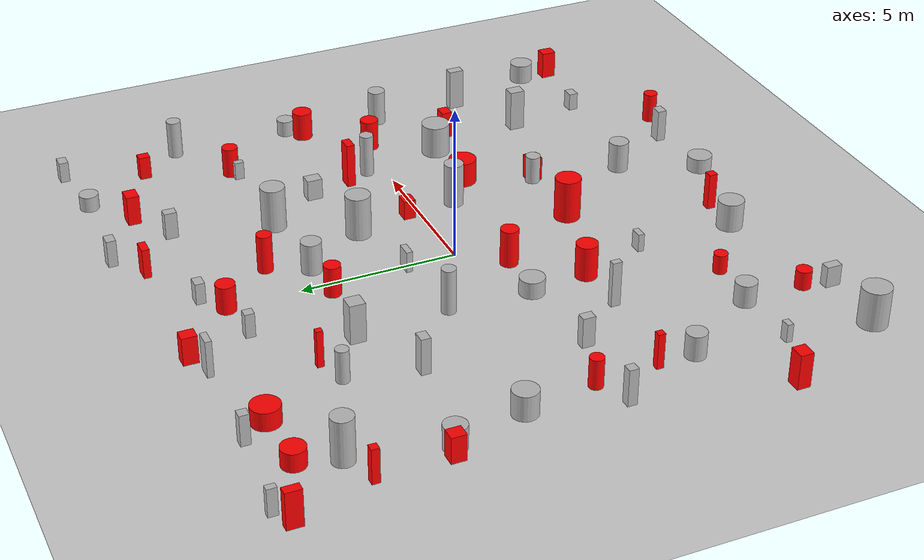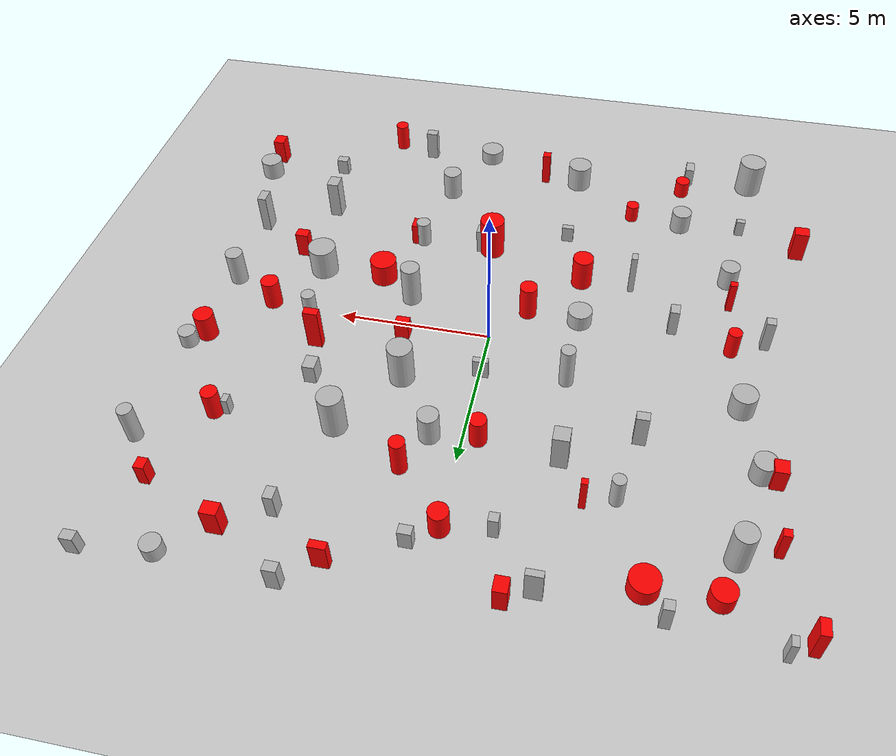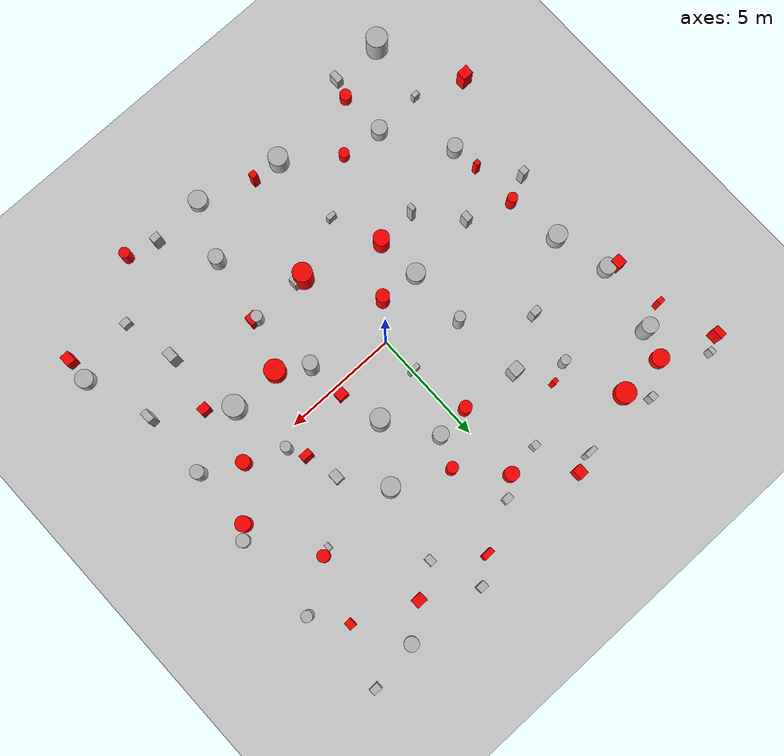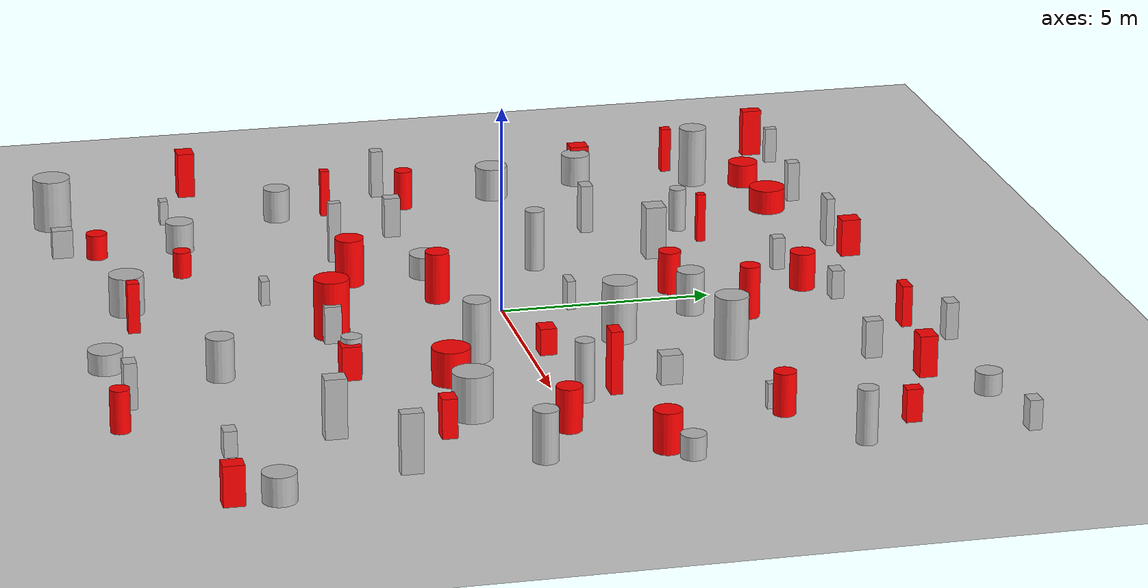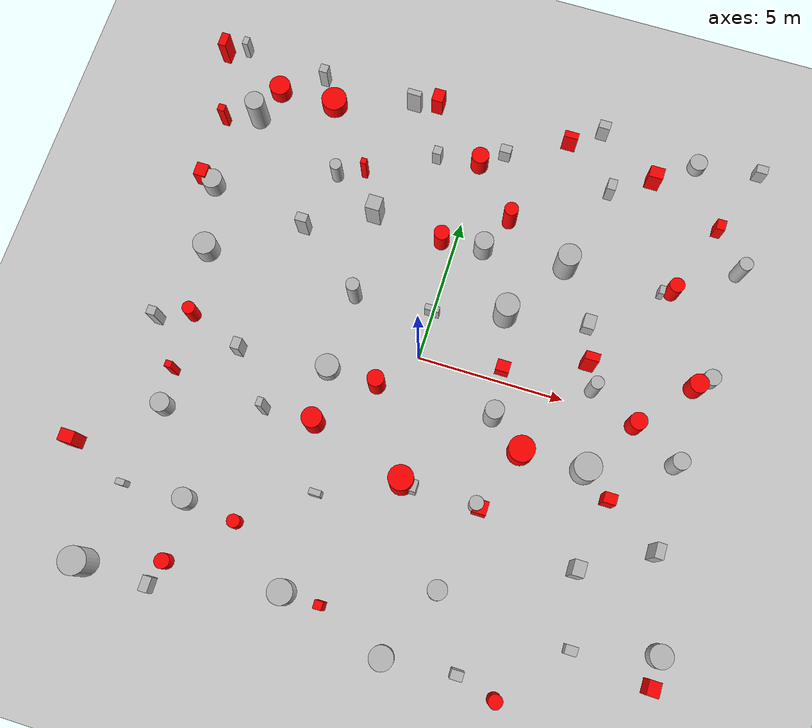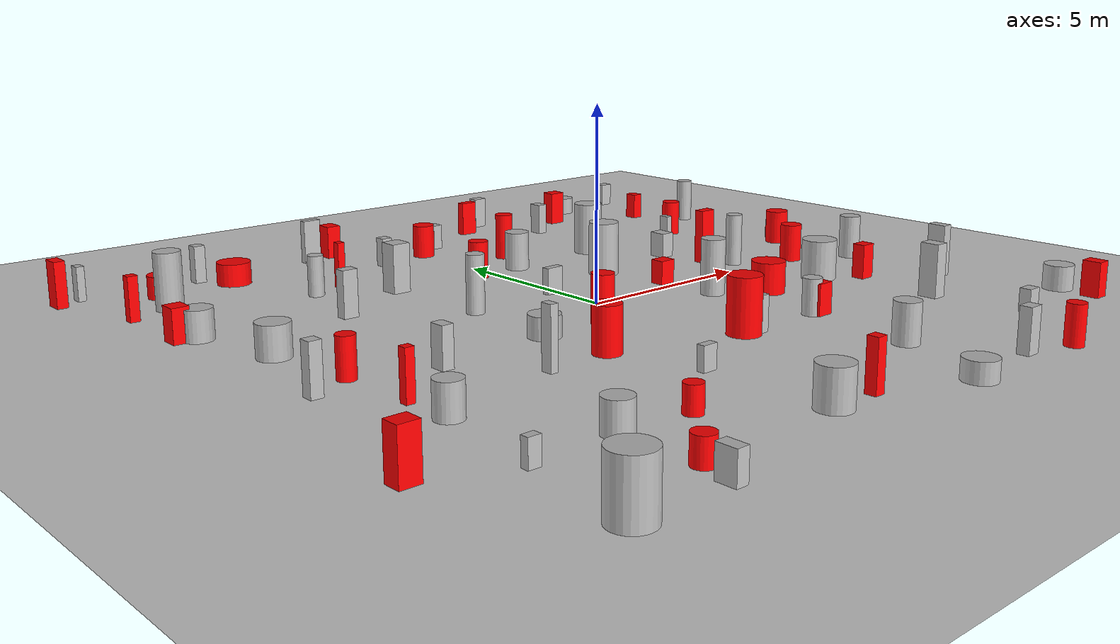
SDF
<sdf version='1.7'>
            <world name='default'>
                <light name='sun' type='directional'>
                <cast_shadows>1</cast_shadows>
                <pose>0 0 10 0 -0 0</pose>
                <diffuse>0.8 0.8 0.8 1</diffuse>
                <specular>0.2 0.2 0.2 1</specular>
                <attenuation>
                    <range>1000</range>
                    <constant>0.9</constant>
                    <linear>0.01</linear>
                    <quadratic>0.001</quadratic>
                </attenuation>
                <direction>-0.5 0.1 -0.9</direction>
                <spot>
                    <inner_angle>0</inner_angle>
                    <outer_angle>0</outer_angle>
                    <falloff>0</falloff>
                </spot>
                </light>
                <model name='ground_plane'>
                <static>1</static>
                <link name='link'>
                    <collision name='collision'>
                    <geometry>
                        <plane>
                        <normal>0 0 1</normal>
                        <size>100 100</size>
                        </plane>
                    </geometry>
                    <surface>
                        <contact>
                        <collide_bitmask>65535</collide_bitmask>
                        <ode/>
                        </contact>
                        <friction>
                        <ode>
                            <mu>100</mu>
                            <mu2>50</mu2>
                        </ode>
                        <torsional>
                            <ode/>
                        </torsional>
                        </friction>
                        <bounce/>
                    </surface>
                    <max_contacts>10</max_contacts>
                    </collision>
                    <visual name='visual'>
                    <cast_shadows>0</cast_shadows>
                    <geometry>
                        <plane>
                        <normal>0 0 1</normal>
                        <size>100 100</size>
                        </plane>
                    </geometry>
                    <material>
                        <script>
                        <uri>file://media/materials/scripts/gazebo.material</uri>
                        <name>Gazebo/Grey</name>
                        </script>
                    </material>
                    </visual>
                    <self_collide>0</self_collide>
                    <enable_wind>0</enable_wind>
                    <kinematic>0</kinematic>
                </link>
                </model>
                <gravity>0 0 -9.8</gravity>
                <magnetic_field>6e-06 2.3e-05 -4.2e-05</magnetic_field>
                <atmosphere type='adiabatic'/>
                <physics type='ode'>
                <max_step_size>0.001</max_step_size>
                <real_time_factor>1</real_time_factor>
                <real_time_update_rate>1000</real_time_update_rate>
                </physics>
                <scene>
                <ambient>0.4 0.4 0.4 1</ambient>
                <background>0.7 0.7 0.7 1</background>
                <shadows>1</shadows>
                </scene>
                <wind/>
                <spherical_coordinates>
                <surface_model>EARTH_WGS84</surface_model>
                <latitude_deg>0</latitude_deg>
                <longitude_deg>0</longitude_deg>
                <elevation>0</elevation>
                <heading_deg>0</heading_deg>
                </spherical_coordinates>

                            <model name='cylinder_0_0.7_0.7_1.0'>
                            <static>true</static>
                            <pose>0.9762700785464951 4.30378732744839 0.5224415914984484 0 0 0</pose> <!-- X, Y, Z, Roll, Pitch, Yaw -->
                            <link name='link'>
                                <collision name='collision'>
                                    <geometry>
                                        <cylinder>
                                            <radius>0.3270964398016714</radius>
                                            <length>1.0448831829968968</length>
                                        </cylinder>
                                    </geometry>
                                    <surface>
                                        <friction>
                                            <ode>
                                                <mu>1.0</mu>
                                                <mu2>1.0</mu2>
                                            </ode>
                                        </friction>
                                        <contact>
                                            <ode>
                                                <kp>1e+5</kp>
                                                <kd>1</kd>
                                            </ode>
                                        </contact>
                                    </surface>
                                </collision>
                                <visual name='visual'>
                                <geometry>
                                    <cylinder>
                                        <radius>0.3270964398016714</radius>
                                        <length>1.0448831829968968</length>
                                    </cylinder>
                                </geometry>
                                </visual>
                                <inertial>
                                    <mass>1.0</mass>
                                    <inertia>
                                        <ixx>0.145833</ixx>
                                        <ixy>0</ixy>
                                        <ixz>0</ixz>
                                        <iyy>0.145833</iyy>
                                        <iyz>0</iyz>
                                        <izz>0.125</izz>
                                    </inertia>
                                </inertial>
                            </link>
                            </model>

                            <model name='cylinder_1_0.6_0.6_1.5'>
                            <static>true</static>
                            <pose>2.917882261333123 -1.2482557747461502 0.7318313802505146 0 0 0</pose> <!-- X, Y, Z, Roll, Pitch, Yaw -->
                            <link name='link'>
                                <collision name='collision'>
                                    <geometry>
                                        <cylinder>
                                            <radius>0.3150324556477333</radius>
                                            <length>1.4636627605010293</length>
                                        </cylinder>
                                    </geometry>
                                    <surface>
                                        <friction>
                                            <ode>
                                                <mu>1.0</mu>
                                                <mu2>1.0</mu2>
                                            </ode>
                                        </friction>
                                        <contact>
                                            <ode>
                                                <kp>1e+5</kp>
                                                <kd>1</kd>
                                            </ode>
                                        </contact>
                                    </surface>
                                </collision>
                                <visual name='visual'>
                                <geometry>
                                    <cylinder>
                                        <radius>0.3150324556477333</radius>
                                        <length>1.4636627605010293</length>
                                    </cylinder>
                                </geometry>
                                </visual>
                                <inertial>
                                    <mass>1.0</mass>
                                    <inertia>
                                        <ixx>0.145833</ixx>
                                        <ixy>0</ixy>
                                        <ixz>0</ixz>
                                        <iyy>0.145833</iyy>
                                        <iyz>0</iyz>
                                        <izz>0.125</izz>
                                    </inertia>
                                </inertial>
                            </link>
                            </model>

                            <model name='cylinder_2_0.4_0.4_1.4'>
                            <static>true</static>
                            <pose>5.834500761653292 0.5778983950580887 0.7127983191463305 0 0 0</pose> <!-- X, Y, Z, Roll, Pitch, Yaw -->
                            <link name='link'>
                                <collision name='collision'>
                                    <geometry>
                                        <cylinder>
                                            <radius>0.2213108174593661</radius>
                                            <length>1.425596638292661</length>
                                        </cylinder>
                                    </geometry>
                                    <surface>
                                        <friction>
                                            <ode>
                                                <mu>1.0</mu>
                                                <mu2>1.0</mu2>
                                            </ode>
                                        </friction>
                                        <contact>
                                            <ode>
                                                <kp>1e+5</kp>
                                                <kd>1</kd>
                                            </ode>
                                        </contact>
                                    </surface>
                                </collision>
                                <visual name='visual'>
                                <geometry>
                                    <cylinder>
                                        <radius>0.2213108174593661</radius>
                                        <length>1.425596638292661</length>
                                    </cylinder>
                                </geometry>
                                </visual>
                                <inertial>
                                    <mass>1.0</mass>
                                    <inertia>
                                        <ixx>0.145833</ixx>
                                        <ixy>0</ixy>
                                        <ixz>0</ixz>
                                        <iyy>0.145833</iyy>
                                        <iyz>0</iyz>
                                        <izz>0.125</izz>
                                    </inertia>
                                </inertial>
                            </link>
                            </model>

                            <model name='cylinder_3_0.9_0.9_1.3'>
                            <static>true</static>
                            <pose>-8.257414005969185 -9.595632051193485 0.6390783754749252 0 0 0</pose> <!-- X, Y, Z, Roll, Pitch, Yaw -->
                            <link name='link'>
                                <collision name='collision'>
                                    <geometry>
                                        <cylinder>
                                            <radius>0.46100364447404574</radius>
                                            <length>1.2781567509498504</length>
                                        </cylinder>
                                    </geometry>
                                    <surface>
                                        <friction>
                                            <ode>
                                                <mu>1.0</mu>
                                                <mu2>1.0</mu2>
                                            </ode>
                                        </friction>
                                        <contact>
                                            <ode>
                                                <kp>1e+5</kp>
                                                <kd>1</kd>
                                            </ode>
                                        </contact>
                                    </surface>
                                </collision>
                                <visual name='visual'>
                                <geometry>
                                    <cylinder>
                                        <radius>0.46100364447404574</radius>
                                        <length>1.2781567509498504</length>
                                    </cylinder>
                                </geometry>
                                </visual>
                                <inertial>
                                    <mass>1.0</mass>
                                    <inertia>
                                        <ixx>0.145833</ixx>
                                        <ixy>0</ixy>
                                        <ixz>0</ixz>
                                        <iyy>0.145833</iyy>
                                        <iyz>0</iyz>
                                        <izz>0.125</izz>
                                    </inertia>
                                </inertial>
                            </link>
                            </model>

                            <model name='cylinder_4_0.5_0.5_1.3'>
                            <static>true</static>
                            <pose>9.572366844655281 5.983171284334471 0.6402645881432277 0 0 0</pose> <!-- X, Y, Z, Roll, Pitch, Yaw -->
                            <link name='link'>
                                <collision name='collision'>
                                    <geometry>
                                        <cylinder>
                                            <radius>0.23548232776067998</radius>
                                            <length>1.2805291762864555</length>
                                        </cylinder>
                                    </geometry>
                                    <surface>
                                        <friction>
                                            <ode>
                                                <mu>1.0</mu>
                                                <mu2>1.0</mu2>
                                            </ode>
                                        </friction>
                                        <contact>
                                            <ode>
                                                <kp>1e+5</kp>
                                                <kd>1</kd>
                                            </ode>
                                        </contact>
                                    </surface>
                                </collision>
                                <visual name='visual'>
                                <geometry>
                                    <cylinder>
                                        <radius>0.23548232776067998</radius>
                                        <length>1.2805291762864555</length>
                                    </cylinder>
                                </geometry>
                                </visual>
                                <inertial>
                                    <mass>1.0</mass>
                                    <inertia>
                                        <ixx>0.145833</ixx>
                                        <ixy>0</ixy>
                                        <ixz>0</ixz>
                                        <iyy>0.145833</iyy>
                                        <iyz>0</iyz>
                                        <izz>0.125</izz>
                                    </inertia>
                                </inertial>
                            </link>
                            </model>

                            <model name='cylinder_5_0.6_0.6_1.0'>
                            <static>true</static>
                            <pose>2.798420426550477 -7.132934251819072 0.5109241608750359 0 0 0</pose> <!-- X, Y, Z, Roll, Pitch, Yaw -->
                            <link name='link'>
                                <collision name='collision'>
                                    <geometry>
                                        <cylinder>
                                            <radius>0.3243985819971571</radius>
                                            <length>1.0218483217500718</length>
                                        </cylinder>
                                    </geometry>
                                    <surface>
                                        <friction>
                                            <ode>
                                                <mu>1.0</mu>
                                                <mu2>1.0</mu2>
                                            </ode>
                                        </friction>
                                        <contact>
                                            <ode>
                                                <kp>1e+5</kp>
                                                <kd>1</kd>
                                            </ode>
                                        </contact>
                                    </surface>
                                </collision>
                                <visual name='visual'>
                                <geometry>
                                    <cylinder>
                                        <radius>0.3243985819971571</radius>
                                        <length>1.0218483217500718</length>
                                    </cylinder>
                                </geometry>
                                </visual>
                                <inertial>
                                    <mass>1.0</mass>
                                    <inertia>
                                        <ixx>0.145833</ixx>
                                        <ixy>0</ixy>
                                        <ixz>0</ixz>
                                        <iyy>0.145833</iyy>
                                        <iyz>0</iyz>
                                        <izz>0.125</izz>
                                    </inertia>
                                </inertial>
                            </link>
                            </model>

                            <model name='cylinder_6_0.4_0.4_1.1'>
                            <static>true</static>
                            <pose>-4.70888775790746 5.484673788684333 0.5342169744343243 0 0 0</pose> <!-- X, Y, Z, Roll, Pitch, Yaw -->
                            <link name='link'>
                                <collision name='collision'>
                                    <geometry>
                                        <cylinder>
                                            <radius>0.20563694013090655</radius>
                                            <length>1.0684339488686485</length>
                                        </cylinder>
                                    </geometry>
                                    <surface>
                                        <friction>
                                            <ode>
                                                <mu>1.0</mu>
                                                <mu2>1.0</mu2>
                                            </ode>
                                        </friction>
                                        <contact>
                                            <ode>
                                                <kp>1e+5</kp>
                                                <kd>1</kd>
                                            </ode>
                                        </contact>
                                    </surface>
                                </collision>
                                <visual name='visual'>
                                <geometry>
                                    <cylinder>
                                        <radius>0.20563694013090655</radius>
                                        <length>1.0684339488686485</length>
                                    </cylinder>
                                </geometry>
                                </visual>
                                <inertial>
                                    <mass>1.0</mass>
                                    <inertia>
                                        <ixx>0.145833</ixx>
                                        <ixy>0</ixy>
                                        <ixz>0</ixz>
                                        <iyy>0.145833</iyy>
                                        <iyz>0</iyz>
                                        <izz>0.125</izz>
                                    </inertia>
                                </inertial>
                            </link>
                            </model>

                            <model name='cylinder_7_0.8_0.8_1.4'>
                            <static>true</static>
                            <pose>2.352709941517542 2.2419144544484286 0.7218740392573121 0 0 0</pose> <!-- X, Y, Z, Roll, Pitch, Yaw -->
                            <link name='link'>
                                <collision name='collision'>
                                    <geometry>
                                        <cylinder>
                                            <radius>0.404546089731045</radius>
                                            <length>1.4437480785146242</length>
                                        </cylinder>
                                    </geometry>
                                    <surface>
                                        <friction>
                                            <ode>
                                                <mu>1.0</mu>
                                                <mu2>1.0</mu2>
                                            </ode>
                                        </friction>
                                        <contact>
                                            <ode>
                                                <kp>1e+5</kp>
                                                <kd>1</kd>
                                            </ode>
                                        </contact>
                                    </surface>
                                </collision>
                                <visual name='visual'>
                                <geometry>
                                    <cylinder>
                                        <radius>0.404546089731045</radius>
                                        <length>1.4437480785146242</length>
                                    </cylinder>
                                </geometry>
                                </visual>
                                <inertial>
                                    <mass>1.0</mass>
                                    <inertia>
                                        <ixx>0.145833</ixx>
                                        <ixy>0</ixy>
                                        <ixz>0</ixz>
                                        <iyy>0.145833</iyy>
                                        <iyz>0</iyz>
                                        <izz>0.125</izz>
                                    </inertia>
                                </inertial>
                            </link>
                            </model>

                            <model name='cylinder_8_0.8_0.8_0.6'>
                            <static>true</static>
                            <pose>-2.80984198852428 -1.259360924013171 0.2801127358146349 0 0 0</pose> <!-- X, Y, Z, Roll, Pitch, Yaw -->
                            <link name='link'>
                                <collision name='collision'>
                                    <geometry>
                                        <cylinder>
                                            <radius>0.4000300146337003</radius>
                                            <length>0.5602254716292698</length>
                                        </cylinder>
                                    </geometry>
                                    <surface>
                                        <friction>
                                            <ode>
                                                <mu>1.0</mu>
                                                <mu2>1.0</mu2>
                                            </ode>
                                        </friction>
                                        <contact>
                                            <ode>
                                                <kp>1e+5</kp>
                                                <kd>1</kd>
                                            </ode>
                                        </contact>
                                    </surface>
                                </collision>
                                <visual name='visual'>
                                <geometry>
                                    <cylinder>
                                        <radius>0.4000300146337003</radius>
                                        <length>0.5602254716292698</length>
                                    </cylinder>
                                </geometry>
                                </visual>
                                <inertial>
                                    <mass>1.0</mass>
                                    <inertia>
                                        <ixx>0.145833</ixx>
                                        <ixy>0</ixy>
                                        <ixz>0</ixz>
                                        <iyy>0.145833</iyy>
                                        <iyz>0</iyz>
                                        <izz>0.125</izz>
                                    </inertia>
                                </inertial>
                            </link>
                            </model>

                            <model name='cylinder_9_0.5_0.5_1.5'>
                            <static>true</static>
                            <pose>-2.725784581147548 1.4039354083575937 0.7441869190296131 0 0 0</pose> <!-- X, Y, Z, Roll, Pitch, Yaw -->
                            <link name='link'>
                                <collision name='collision'>
                                    <geometry>
                                        <cylinder>
                                            <radius>0.23061344322440844</radius>
                                            <length>1.4883738380592262</length>
                                        </cylinder>
                                    </geometry>
                                    <surface>
                                        <friction>
                                            <ode>
                                                <mu>1.0</mu>
                                                <mu2>1.0</mu2>
                                            </ode>
                                        </friction>
                                        <contact>
                                            <ode>
                                                <kp>1e+5</kp>
                                                <kd>1</kd>
                                            </ode>
                                        </contact>
                                    </surface>
                                </collision>
                                <visual name='visual'>
                                <geometry>
                                    <cylinder>
                                        <radius>0.23061344322440844</radius>
                                        <length>1.4883738380592262</length>
                                    </cylinder>
                                </geometry>
                                </visual>
                                <inertial>
                                    <mass>1.0</mass>
                                    <inertia>
                                        <ixx>0.145833</ixx>
                                        <ixy>0</ixy>
                                        <ixz>0</ixz>
                                        <iyy>0.145833</iyy>
                                        <iyz>0</iyz>
                                        <izz>0.125</izz>
                                    </inertia>
                                </inertial>
                            </link>
                            </model>

                            <model name='cylinder_10_0.7_0.7_0.8'>
                            <static>true</static>
                            <pose>-5.822464878103306 -6.773809642300074 0.37664580126989106 0 0 0</pose> <!-- X, Y, Z, Roll, Pitch, Yaw -->
                            <link name='link'>
                                <collision name='collision'>
                                    <geometry>
                                        <cylinder>
                                            <radius>0.3398932318568919</radius>
                                            <length>0.7532916025397821</length>
                                        </cylinder>
                                    </geometry>
                                    <surface>
                                        <friction>
                                            <ode>
                                                <mu>1.0</mu>
                                                <mu2>1.0</mu2>
                                            </ode>
                                        </friction>
                                        <contact>
                                            <ode>
                                                <kp>1e+5</kp>
                                                <kd>1</kd>
                                            </ode>
                                        </contact>
                                    </surface>
                                </collision>
                                <visual name='visual'>
                                <geometry>
                                    <cylinder>
                                        <radius>0.3398932318568919</radius>
                                        <length>0.7532916025397821</length>
                                    </cylinder>
                                </geometry>
                                </visual>
                                <inertial>
                                    <mass>1.0</mass>
                                    <inertia>
                                        <ixx>0.145833</ixx>
                                        <ixy>0</ixy>
                                        <ixz>0</ixz>
                                        <iyy>0.145833</iyy>
                                        <iyz>0</iyz>
                                        <izz>0.125</izz>
                                    </inertia>
                                </inertial>
                            </link>
                            </model>

                            <model name='cylinder_11_0.7_0.7_1.5'>
                            <static>true</static>
                            <pose>-8.057974484138775 6.758898149976076 0.7382297325066979 0 0 0</pose> <!-- X, Y, Z, Roll, Pitch, Yaw -->
                            <link name='link'>
                                <collision name='collision'>
                                    <geometry>
                                        <cylinder>
                                            <radius>0.3405953604943105</radius>
                                            <length>1.4764594650133958</length>
                                        </cylinder>
                                    </geometry>
                                    <surface>
                                        <friction>
                                            <ode>
                                                <mu>1.0</mu>
                                                <mu2>1.0</mu2>
                                            </ode>
                                        </friction>
                                        <contact>
                                            <ode>
                                                <kp>1e+5</kp>
                                                <kd>1</kd>
                                            </ode>
                                        </contact>
                                    </surface>
                                </collision>
                                <visual name='visual'>
                                <geometry>
                                    <cylinder>
                                        <radius>0.3405953604943105</radius>
                                        <length>1.4764594650133958</length>
                                    </cylinder>
                                </geometry>
                                </visual>
                                <inertial>
                                    <mass>1.0</mass>
                                    <inertia>
                                        <ixx>0.145833</ixx>
                                        <ixy>0</ixy>
                                        <ixz>0</ixz>
                                        <iyy>0.145833</iyy>
                                        <iyz>0</iyz>
                                        <izz>0.125</izz>
                                    </inertia>
                                </inertial>
                            </link>
                            </model>

                            <model name='cylinder_12_0.6_0.6_0.5'>
                            <static>true</static>
                            <pose>9.535221763806742 2.0969103949009202 0.26959389612716034 0 0 0</pose> <!-- X, Y, Z, Roll, Pitch, Yaw -->
                            <link name='link'>
                                <collision name='collision'>
                                    <geometry>
                                        <cylinder>
                                            <radius>0.2848420887729229</radius>
                                            <length>0.5391877922543207</length>
                                        </cylinder>
                                    </geometry>
                                    <surface>
                                        <friction>
                                            <ode>
                                                <mu>1.0</mu>
                                                <mu2>1.0</mu2>
                                            </ode>
                                        </friction>
                                        <contact>
                                            <ode>
                                                <kp>1e+5</kp>
                                                <kd>1</kd>
                                            </ode>
                                        </contact>
                                    </surface>
                                </collision>
                                <visual name='visual'>
                                <geometry>
                                    <cylinder>
                                        <radius>0.2848420887729229</radius>
                                        <length>0.5391877922543207</length>
                                    </cylinder>
                                </geometry>
                                </visual>
                                <inertial>
                                    <mass>1.0</mass>
                                    <inertia>
                                        <ixx>0.145833</ixx>
                                        <ixy>0</ixy>
                                        <ixz>0</ixz>
                                        <iyy>0.145833</iyy>
                                        <iyz>0</iyz>
                                        <izz>0.125</izz>
                                    </inertia>
                                </inertial>
                            </link>
                            </model>

                            <model name='cylinder_13_0.6_0.6_0.8'>
                            <static>true</static>
                            <pose>-7.596068775736622 -4.077196049557101 0.408991589696988 0 0 0</pose> <!-- X, Y, Z, Roll, Pitch, Yaw -->
                            <link name='link'>
                                <collision name='collision'>
                                    <geometry>
                                        <cylinder>
                                            <radius>0.324278898354401</radius>
                                            <length>0.817983179393976</length>
                                        </cylinder>
                                    </geometry>
                                    <surface>
                                        <friction>
                                            <ode>
                                                <mu>1.0</mu>
                                                <mu2>1.0</mu2>
                                            </ode>
                                        </friction>
                                        <contact>
                                            <ode>
                                                <kp>1e+5</kp>
                                                <kd>1</kd>
                                            </ode>
                                        </contact>
                                    </surface>
                                </collision>
                                <visual name='visual'>
                                <geometry>
                                    <cylinder>
                                        <radius>0.324278898354401</radius>
                                        <length>0.817983179393976</length>
                                    </cylinder>
                                </geometry>
                                </visual>
                                <inertial>
                                    <mass>1.0</mass>
                                    <inertia>
                                        <ixx>0.145833</ixx>
                                        <ixy>0</ixy>
                                        <ixz>0</ixz>
                                        <iyy>0.145833</iyy>
                                        <iyz>0</iyz>
                                        <izz>0.125</izz>
                                    </inertia>
                                </inertial>
                            </link>
                            </model>

                            <model name='cylinder_14_0.7_0.7_0.8'>
                            <static>true</static>
                            <pose>-8.717050073024312 3.849442387400398 0.3826947454697227 0 0 0</pose> <!-- X, Y, Z, Roll, Pitch, Yaw -->
                            <link name='link'>
                                <collision name='collision'>
                                    <geometry>
                                        <cylinder>
                                            <radius>0.3569744160400099</radius>
                                            <length>0.7653894909394454</length>
                                        </cylinder>
                                    </geometry>
                                    <surface>
                                        <friction>
                                            <ode>
                                                <mu>1.0</mu>
                                                <mu2>1.0</mu2>
                                            </ode>
                                        </friction>
                                        <contact>
                                            <ode>
                                                <kp>1e+5</kp>
                                                <kd>1</kd>
                                            </ode>
                                        </contact>
                                    </surface>
                                </collision>
                                <visual name='visual'>
                                <geometry>
                                    <cylinder>
                                        <radius>0.3569744160400099</radius>
                                        <length>0.7653894909394454</length>
                                    </cylinder>
                                </geometry>
                                </visual>
                                <inertial>
                                    <mass>1.0</mass>
                                    <inertia>
                                        <ixx>0.145833</ixx>
                                        <ixy>0</ixy>
                                        <ixz>0</ixz>
                                        <iyy>0.145833</iyy>
                                        <iyz>0</iyz>
                                        <izz>0.125</izz>
                                    </inertia>
                                </inertial>
                            </link>
                            </model>

                            <model name='cylinder_15_0.8_0.8_0.8'>
                            <static>true</static>
                            <pose>-8.121189784831166 1.5189299111235854 0.40928447622566183 0 0 0</pose> <!-- X, Y, Z, Roll, Pitch, Yaw -->
                            <link name='link'>
                                <collision name='collision'>
                                    <geometry>
                                        <cylinder>
                                            <radius>0.4002231139891045</radius>
                                            <length>0.8185689524513237</length>
                                        </cylinder>
                                    </geometry>
                                    <surface>
                                        <friction>
                                            <ode>
                                                <mu>1.0</mu>
                                                <mu2>1.0</mu2>
                                            </ode>
                                        </friction>
                                        <contact>
                                            <ode>
                                                <kp>1e+5</kp>
                                                <kd>1</kd>
                                            </ode>
                                        </contact>
                                    </surface>
                                </collision>
                                <visual name='visual'>
                                <geometry>
                                    <cylinder>
                                        <radius>0.4002231139891045</radius>
                                        <length>0.8185689524513237</length>
                                    </cylinder>
                                </geometry>
                                </visual>
                                <inertial>
                                    <mass>1.0</mass>
                                    <inertia>
                                        <ixx>0.145833</ixx>
                                        <ixy>0</ixy>
                                        <ixz>0</ixz>
                                        <iyy>0.145833</iyy>
                                        <iyz>0</iyz>
                                        <izz>0.125</izz>
                                    </inertia>
                                </inertial>
                            </link>
                            </model>

                            <model name='cylinder_16_0.8_0.8_0.5'>
                            <static>true</static>
                            <pose>1.7302586962016626 -9.597849076250128 0.25234773809627353 0 0 0</pose> <!-- X, Y, Z, Roll, Pitch, Yaw -->
                            <link name='link'>
                                <collision name='collision'>
                                    <geometry>
                                        <cylinder>
                                            <radius>0.4033449610388691</radius>
                                            <length>0.5046954761925471</length>
                                        </cylinder>
                                    </geometry>
                                    <surface>
                                        <friction>
                                            <ode>
                                                <mu>1.0</mu>
                                                <mu2>1.0</mu2>
                                            </ode>
                                        </friction>
                                        <contact>
                                            <ode>
                                                <kp>1e+5</kp>
                                                <kd>1</kd>
                                            </ode>
                                        </contact>
                                    </surface>
                                </collision>
                                <visual name='visual'>
                                <geometry>
                                    <cylinder>
                                        <radius>0.4033449610388691</radius>
                                        <length>0.5046954761925471</length>
                                    </cylinder>
                                </geometry>
                                </visual>
                                <inertial>
                                    <mass>1.0</mass>
                                    <inertia>
                                        <ixx>0.145833</ixx>
                                        <ixy>0</ixy>
                                        <ixz>0</ixz>
                                        <iyy>0.145833</iyy>
                                        <iyz>0</iyz>
                                        <izz>0.125</izz>
                                    </inertia>
                                </inertial>
                            </link>
                            </model>

                            <model name='cylinder_17_0.6_0.6_1.2'>
                            <static>true</static>
                            <pose>9.054980230339702 -1.0574924276474533 0.5997396376587522 0 0 0</pose> <!-- X, Y, Z, Roll, Pitch, Yaw -->
                            <link name='link'>
                                <collision name='collision'>
                                    <geometry>
                                        <cylinder>
                                            <radius>0.2892310852565401</radius>
                                            <length>1.1994792753175043</length>
                                        </cylinder>
                                    </geometry>
                                    <surface>
                                        <friction>
                                            <ode>
                                                <mu>1.0</mu>
                                                <mu2>1.0</mu2>
                                            </ode>
                                        </friction>
                                        <contact>
                                            <ode>
                                                <kp>1e+5</kp>
                                                <kd>1</kd>
                                            </ode>
                                        </contact>
                                    </surface>
                                </collision>
                                <visual name='visual'>
                                <geometry>
                                    <cylinder>
                                        <radius>0.2892310852565401</radius>
                                        <length>1.1994792753175043</length>
                                    </cylinder>
                                </geometry>
                                </visual>
                                <inertial>
                                    <mass>1.0</mass>
                                    <inertia>
                                        <ixx>0.145833</ixx>
                                        <ixy>0</ixy>
                                        <ixz>0</ixz>
                                        <iyy>0.145833</iyy>
                                        <iyz>0</iyz>
                                        <izz>0.125</izz>
                                    </inertia>
                                </inertial>
                            </link>
                            </model>

                            <model name='cylinder_18_0.9_0.9_1.1'>
                            <static>true</static>
                            <pose>6.275956394049544 -2.0698851830603076 0.5406364363179293 0 0 0</pose> <!-- X, Y, Z, Roll, Pitch, Yaw -->
                            <link name='link'>
                                <collision name='collision'>
                                    <geometry>
                                        <cylinder>
                                            <radius>0.4645206085564558</radius>
                                            <length>1.0812728726358587</length>
                                        </cylinder>
                                    </geometry>
                                    <surface>
                                        <friction>
                                            <ode>
                                                <mu>1.0</mu>
                                                <mu2>1.0</mu2>
                                            </ode>
                                        </friction>
                                        <contact>
                                            <ode>
                                                <kp>1e+5</kp>
                                                <kd>1</kd>
                                            </ode>
                                        </contact>
                                    </surface>
                                </collision>
                                <visual name='visual'>
                                <geometry>
                                    <cylinder>
                                        <radius>0.4645206085564558</radius>
                                        <length>1.0812728726358587</length>
                                    </cylinder>
                                </geometry>
                                </visual>
                                <inertial>
                                    <mass>1.0</mass>
                                    <inertia>
                                        <ixx>0.145833</ixx>
                                        <ixy>0</ixy>
                                        <ixz>0</ixz>
                                        <iyy>0.145833</iyy>
                                        <iyz>0</iyz>
                                        <izz>0.125</izz>
                                    </inertia>
                                </inertial>
                            </link>
                            </model>

                            <model name='cylinder_19_0.8_0.8_1.5'>
                            <static>true</static>
                            <pose>3.850631801555318 4.50508559639281 0.7280418173616119 0 0 0</pose> <!-- X, Y, Z, Roll, Pitch, Yaw -->
                            <link name='link'>
                                <collision name='collision'>
                                    <geometry>
                                        <cylinder>
                                            <radius>0.3931970597688912</radius>
                                            <length>1.4560836347232238</length>
                                        </cylinder>
                                    </geometry>
                                    <surface>
                                        <friction>
                                            <ode>
                                                <mu>1.0</mu>
                                                <mu2>1.0</mu2>
                                            </ode>
                                        </friction>
                                        <contact>
                                            <ode>
                                                <kp>1e+5</kp>
                                                <kd>1</kd>
                                            </ode>
                                        </contact>
                                    </surface>
                                </collision>
                                <visual name='visual'>
                                <geometry>
                                    <cylinder>
                                        <radius>0.3931970597688912</radius>
                                        <length>1.4560836347232238</length>
                                    </cylinder>
                                </geometry>
                                </visual>
                                <inertial>
                                    <mass>1.0</mass>
                                    <inertia>
                                        <ixx>0.145833</ixx>
                                        <ixy>0</ixy>
                                        <ixz>0</ixz>
                                        <iyy>0.145833</iyy>
                                        <iyz>0</iyz>
                                        <izz>0.125</izz>
                                    </inertia>
                                </inertial>
                            </link>
                            </model>

                            <model name='cylinder_20_0.5_0.5_0.9'>
                            <static>true</static>
                            <pose>3.2034707498537003 -4.198447855791119 0.46438435047288307 0 0 0</pose> <!-- X, Y, Z, Roll, Pitch, Yaw -->
                            <link name='link'>
                                <collision name='collision'>
                                    <geometry>
                                        <cylinder>
                                            <radius>0.24064221926673507</radius>
                                            <length>0.9287687009457661</length>
                                        </cylinder>
                                    </geometry>
                                    <surface>
                                        <friction>
                                            <ode>
                                                <mu>1.0</mu>
                                                <mu2>1.0</mu2>
                                            </ode>
                                        </friction>
                                        <contact>
                                            <ode>
                                                <kp>1e+5</kp>
                                                <kd>1</kd>
                                            </ode>
                                        </contact>
                                    </surface>
                                </collision>
                                <visual name='visual'>
                                <geometry>
                                    <cylinder>
                                        <radius>0.24064221926673507</radius>
                                        <length>0.9287687009457661</length>
                                    </cylinder>
                                </geometry>
                                </visual>
                                <inertial>
                                    <mass>1.0</mass>
                                    <inertia>
                                        <ixx>0.145833</ixx>
                                        <ixy>0</ixy>
                                        <ixz>0</ixz>
                                        <iyy>0.145833</iyy>
                                        <iyz>0</iyz>
                                        <izz>0.125</izz>
                                    </inertia>
                                </inertial>
                            </link>
                            </model>

                            <model name='cylinder_21_0.8_0.8_0.7'>
                            <static>true</static>
                            <pose>9.976940131357331 -7.011033906840125 0.3312464673381874 0 0 0</pose> <!-- X, Y, Z, Roll, Pitch, Yaw -->
                            <link name='link'>
                                <collision name='collision'>
                                    <geometry>
                                        <cylinder>
                                            <radius>0.3846678692851533</radius>
                                            <length>0.6624929346763748</length>
                                        </cylinder>
                                    </geometry>
                                    <surface>
                                        <friction>
                                            <ode>
                                                <mu>1.0</mu>
                                                <mu2>1.0</mu2>
                                            </ode>
                                        </friction>
                                        <contact>
                                            <ode>
                                                <kp>1e+5</kp>
                                                <kd>1</kd>
                                            </ode>
                                        </contact>
                                    </surface>
                                </collision>
                                <visual name='visual'>
                                <geometry>
                                    <cylinder>
                                        <radius>0.3846678692851533</radius>
                                        <length>0.6624929346763748</length>
                                    </cylinder>
                                </geometry>
                                </visual>
                                <inertial>
                                    <mass>1.0</mass>
                                    <inertia>
                                        <ixx>0.145833</ixx>
                                        <ixy>0</ixy>
                                        <ixz>0</ixz>
                                        <iyy>0.145833</iyy>
                                        <iyz>0</iyz>
                                        <izz>0.125</izz>
                                    </inertia>
                                </inertial>
                            </link>
                            </model>

                            <model name='cylinder_22_0.8_0.8_1.0'>
                            <static>true</static>
                            <pose>-1.8563340554800067 -8.61666009089724 0.4767713413390344 0 0 0</pose> <!-- X, Y, Z, Roll, Pitch, Yaw -->
                            <link name='link'>
                                <collision name='collision'>
                                    <geometry>
                                        <cylinder>
                                            <radius>0.4166166798411044</radius>
                                            <length>0.9535426826780689</length>
                                        </cylinder>
                                    </geometry>
                                    <surface>
                                        <friction>
                                            <ode>
                                                <mu>1.0</mu>
                                                <mu2>1.0</mu2>
                                            </ode>
                                        </friction>
                                        <contact>
                                            <ode>
                                                <kp>1e+5</kp>
                                                <kd>1</kd>
                                            </ode>
                                        </contact>
                                    </surface>
                                </collision>
                                <visual name='visual'>
                                <geometry>
                                    <cylinder>
                                        <radius>0.4166166798411044</radius>
                                        <length>0.9535426826780689</length>
                                    </cylinder>
                                </geometry>
                                </visual>
                                <inertial>
                                    <mass>1.0</mass>
                                    <inertia>
                                        <ixx>0.145833</ixx>
                                        <ixy>0</ixy>
                                        <ixz>0</ixz>
                                        <iyy>0.145833</iyy>
                                        <iyz>0</iyz>
                                        <izz>0.125</izz>
                                    </inertia>
                                </inertial>
                            </link>
                            </model>

                            <model name='cylinder_23_0.6_0.6_0.5'>
                            <static>true</static>
                            <pose>7.327646518572585 9.510430100057718 0.255857042092501 0 0 0</pose> <!-- X, Y, Z, Roll, Pitch, Yaw -->
                            <link name='link'>
                                <collision name='collision'>
                                    <geometry>
                                        <cylinder>
                                            <radius>0.30799341934350916</radius>
                                            <length>0.511714084185002</length>
                                        </cylinder>
                                    </geometry>
                                    <surface>
                                        <friction>
                                            <ode>
                                                <mu>1.0</mu>
                                                <mu2>1.0</mu2>
                                            </ode>
                                        </friction>
                                        <contact>
                                            <ode>
                                                <kp>1e+5</kp>
                                                <kd>1</kd>
                                            </ode>
                                        </contact>
                                    </surface>
                                </collision>
                                <visual name='visual'>
                                <geometry>
                                    <cylinder>
                                        <radius>0.30799341934350916</radius>
                                        <length>0.511714084185002</length>
                                    </cylinder>
                                </geometry>
                                </visual>
                                <inertial>
                                    <mass>1.0</mass>
                                    <inertia>
                                        <ixx>0.145833</ixx>
                                        <ixy>0</ixy>
                                        <ixz>0</ixz>
                                        <iyy>0.145833</iyy>
                                        <iyz>0</iyz>
                                        <izz>0.125</izz>
                                    </inertia>
                                </inertial>
                            </link>
                            </model>

                            <model name='box_0_0.3_0.5_0.7'>
                            <static>true</static>
                            <pose>-6.000069502071998 -9.62956411078772 0.36196234403019006 0 0 0</pose> <!-- X, Y, Z, Roll, Pitch, Yaw -->
                            <link name='link'>
                                <collision name='collision'>
                                    <geometry>
                                        <box>
                                            <size>0.3 0.5 0.7</size>
                                        </box>
                                    </geometry>
                                    <surface>
                                        <friction>
                                            <ode>
                                                <mu>1.0</mu>
                                                <mu2>1.0</mu2>
                                            </ode>
                                        </friction>
                                        <contact>
                                            <ode>
                                                <kp>1e+5</kp>
                                                <kd>1</kd>
                                            </ode>
                                        </contact>
                                    </surface>
                                </collision>
                                <visual name='visual'>
                                <geometry>
                                    <box>
                                        <size>0.3 0.5 0.7</size> <!-- Width, Depth, Height -->
                                    </box>
                                </geometry>
                                </visual>
                                <inertial>
                                    <mass>1.0</mass>
                                    <inertia>
                                        <ixx>0.166667</ixx>
                                        <ixy>0</ixy>
                                        <ixz>0</ixz>
                                        <iyy>0.166667</iyy>
                                        <iyz>0</iyz>
                                        <izz>0.166667</izz>
                                    </inertia>
                                </inertial>
                            </link>
                            </model>

                            <model name='box_1_0.4_0.3_1.1'>
                            <static>true</static>
                            <pose>4.088288038470655 -9.363221409373843 0.5607392007498817 0 0 0</pose> <!-- X, Y, Z, Roll, Pitch, Yaw -->
                            <link name='link'>
                                <collision name='collision'>
                                    <geometry>
                                        <box>
                                            <size>0.4 0.3 1.1</size>
                                        </box>
                                    </geometry>
                                    <surface>
                                        <friction>
                                            <ode>
                                                <mu>1.0</mu>
                                                <mu2>1.0</mu2>
                                            </ode>
                                        </friction>
                                        <contact>
                                            <ode>
                                                <kp>1e+5</kp>
                                                <kd>1</kd>
                                            </ode>
                                        </contact>
                                    </surface>
                                </collision>
                                <visual name='visual'>
                                <geometry>
                                    <box>
                                        <size>0.4 0.3 1.1</size> <!-- Width, Depth, Height -->
                                    </box>
                                </geometry>
                                </visual>
                                <inertial>
                                    <mass>1.0</mass>
                                    <inertia>
                                        <ixx>0.166667</ixx>
                                        <ixy>0</ixy>
                                        <ixz>0</ixz>
                                        <iyy>0.166667</iyy>
                                        <iyz>0</iyz>
                                        <izz>0.166667</izz>
                                    </inertia>
                                </inertial>
                            </link>
                            </model>

                            <model name='box_2_0.3_0.3_1.0'>
                            <static>true</static>
                            <pose>-6.276139882393277 8.887447799678672 0.49522940430878354 0 0 0</pose> <!-- X, Y, Z, Roll, Pitch, Yaw -->
                            <link name='link'>
                                <collision name='collision'>
                                    <geometry>
                                        <box>
                                            <size>0.3 0.3 1.0</size>
                                        </box>
                                    </geometry>
                                    <surface>
                                        <friction>
                                            <ode>
                                                <mu>1.0</mu>
                                                <mu2>1.0</mu2>
                                            </ode>
                                        </friction>
                                        <contact>
                                            <ode>
                                                <kp>1e+5</kp>
                                                <kd>1</kd>
                                            </ode>
                                        </contact>
                                    </surface>
                                </collision>
                                <visual name='visual'>
                                <geometry>
                                    <box>
                                        <size>0.3 0.3 1.0</size> <!-- Width, Depth, Height -->
                                    </box>
                                </geometry>
                                </visual>
                                <inertial>
                                    <mass>1.0</mass>
                                    <inertia>
                                        <ixx>0.166667</ixx>
                                        <ixy>0</ixy>
                                        <ixz>0</ixz>
                                        <iyy>0.166667</iyy>
                                        <iyz>0</iyz>
                                        <izz>0.166667</izz>
                                    </inertia>
                                </inertial>
                            </link>
                            </model>

                            <model name='box_3_0.3_0.3_1.2'>
                            <static>true</static>
                            <pose>-8.839416793522489 -1.3116674888375854 0.5981717444077297 0 0 0</pose> <!-- X, Y, Z, Roll, Pitch, Yaw -->
                            <link name='link'>
                                <collision name='collision'>
                                    <geometry>
                                        <box>
                                            <size>0.3 0.3 1.2</size>
                                        </box>
                                    </geometry>
                                    <surface>
                                        <friction>
                                            <ode>
                                                <mu>1.0</mu>
                                                <mu2>1.0</mu2>
                                            </ode>
                                        </friction>
                                        <contact>
                                            <ode>
                                                <kp>1e+5</kp>
                                                <kd>1</kd>
                                            </ode>
                                        </contact>
                                    </surface>
                                </collision>
                                <visual name='visual'>
                                <geometry>
                                    <box>
                                        <size>0.3 0.3 1.2</size> <!-- Width, Depth, Height -->
                                    </box>
                                </geometry>
                                </visual>
                                <inertial>
                                    <mass>1.0</mass>
                                    <inertia>
                                        <ixx>0.166667</ixx>
                                        <ixy>0</ixy>
                                        <ixz>0</ixz>
                                        <iyy>0.166667</iyy>
                                        <iyz>0</iyz>
                                        <izz>0.166667</izz>
                                    </inertia>
                                </inertial>
                            </link>
                            </model>

                            <model name='box_4_0.4_0.3_0.7'>
                            <static>true</static>
                            <pose>0.731584222174444 7.933425860806842 0.35844849219923697 0 0 0</pose> <!-- X, Y, Z, Roll, Pitch, Yaw -->
                            <link name='link'>
                                <collision name='collision'>
                                    <geometry>
                                        <box>
                                            <size>0.4 0.3 0.7</size>
                                        </box>
                                    </geometry>
                                    <surface>
                                        <friction>
                                            <ode>
                                                <mu>1.0</mu>
                                                <mu2>1.0</mu2>
                                            </ode>
                                        </friction>
                                        <contact>
                                            <ode>
                                                <kp>1e+5</kp>
                                                <kd>1</kd>
                                            </ode>
                                        </contact>
                                    </surface>
                                </collision>
                                <visual name='visual'>
                                <geometry>
                                    <box>
                                        <size>0.4 0.3 0.7</size> <!-- Width, Depth, Height -->
                                    </box>
                                </geometry>
                                </visual>
                                <inertial>
                                    <mass>1.0</mass>
                                    <inertia>
                                        <ixx>0.166667</ixx>
                                        <ixy>0</ixy>
                                        <ixz>0</ixz>
                                        <iyy>0.166667</iyy>
                                        <iyz>0</iyz>
                                        <izz>0.166667</izz>
                                    </inertia>
                                </inertial>
                            </link>
                            </model>

                            <model name='box_5_0.3_0.4_1.0'>
                            <static>true</static>
                            <pose>-5.850598491177812 -1.5062906249698749 0.48178771218240535 0 0 0</pose> <!-- X, Y, Z, Roll, Pitch, Yaw -->
                            <link name='link'>
                                <collision name='collision'>
                                    <geometry>
                                        <box>
                                            <size>0.3 0.4 1.0</size>
                                        </box>
                                    </geometry>
                                    <surface>
                                        <friction>
                                            <ode>
                                                <mu>1.0</mu>
                                                <mu2>1.0</mu2>
                                            </ode>
                                        </friction>
                                        <contact>
                                            <ode>
                                                <kp>1e+5</kp>
                                                <kd>1</kd>
                                            </ode>
                                        </contact>
                                    </surface>
                                </collision>
                                <visual name='visual'>
                                <geometry>
                                    <box>
                                        <size>0.3 0.4 1.0</size> <!-- Width, Depth, Height -->
                                    </box>
                                </geometry>
                                </visual>
                                <inertial>
                                    <mass>1.0</mass>
                                    <inertia>
                                        <ixx>0.166667</ixx>
                                        <ixy>0</ixy>
                                        <ixz>0</ixz>
                                        <iyy>0.166667</iyy>
                                        <iyz>0</iyz>
                                        <izz>0.166667</izz>
                                    </inertia>
                                </inertial>
                            </link>
                            </model>

                            <model name='box_6_0.4_0.3_0.6'>
                            <static>true</static>
                            <pose>7.277112118464629 -7.649362880759338 0.31603405317257666 0 0 0</pose> <!-- X, Y, Z, Roll, Pitch, Yaw -->
                            <link name='link'>
                                <collision name='collision'>
                                    <geometry>
                                        <box>
                                            <size>0.4 0.3 0.6</size>
                                        </box>
                                    </geometry>
                                    <surface>
                                        <friction>
                                            <ode>
                                                <mu>1.0</mu>
                                                <mu2>1.0</mu2>
                                            </ode>
                                        </friction>
                                        <contact>
                                            <ode>
                                                <kp>1e+5</kp>
                                                <kd>1</kd>
                                            </ode>
                                        </contact>
                                    </surface>
                                </collision>
                                <visual name='visual'>
                                <geometry>
                                    <box>
                                        <size>0.4 0.3 0.6</size> <!-- Width, Depth, Height -->
                                    </box>
                                </geometry>
                                </visual>
                                <inertial>
                                    <mass>1.0</mass>
                                    <inertia>
                                        <ixx>0.166667</ixx>
                                        <ixy>0</ixy>
                                        <ixz>0</ixz>
                                        <iyy>0.166667</iyy>
                                        <iyz>0</iyz>
                                        <izz>0.166667</izz>
                                    </inertia>
                                </inertial>
                            </link>
                            </model>

                            <model name='box_7_0.5_0.2_1.2'>
                            <static>true</static>
                            <pose>-2.8877452430008876 8.80863890505626 0.6243318099252737 0 0 0</pose> <!-- X, Y, Z, Roll, Pitch, Yaw -->
                            <link name='link'>
                                <collision name='collision'>
                                    <geometry>
                                        <box>
                                            <size>0.5 0.2 1.2</size>
                                        </box>
                                    </geometry>
                                    <surface>
                                        <friction>
                                            <ode>
                                                <mu>1.0</mu>
                                                <mu2>1.0</mu2>
                                            </ode>
                                        </friction>
                                        <contact>
                                            <ode>
                                                <kp>1e+5</kp>
                                                <kd>1</kd>
                                            </ode>
                                        </contact>
                                    </surface>
                                </collision>
                                <visual name='visual'>
                                <geometry>
                                    <box>
                                        <size>0.5 0.2 1.2</size> <!-- Width, Depth, Height -->
                                    </box>
                                </geometry>
                                </visual>
                                <inertial>
                                    <mass>1.0</mass>
                                    <inertia>
                                        <ixx>0.166667</ixx>
                                        <ixy>0</ixy>
                                        <ixz>0</ixz>
                                        <iyy>0.166667</iyy>
                                        <iyz>0</iyz>
                                        <izz>0.166667</izz>
                                    </inertia>
                                </inertial>
                            </link>
                            </model>

                            <model name='box_8_0.4_0.2_0.6'>
                            <static>true</static>
                            <pose>-1.8551765717238524 -5.355317156581146 0.27671359089341263 0 0 0</pose> <!-- X, Y, Z, Roll, Pitch, Yaw -->
                            <link name='link'>
                                <collision name='collision'>
                                    <geometry>
                                        <box>
                                            <size>0.4 0.2 0.6</size>
                                        </box>
                                    </geometry>
                                    <surface>
                                        <friction>
                                            <ode>
                                                <mu>1.0</mu>
                                                <mu2>1.0</mu2>
                                            </ode>
                                        </friction>
                                        <contact>
                                            <ode>
                                                <kp>1e+5</kp>
                                                <kd>1</kd>
                                            </ode>
                                        </contact>
                                    </surface>
                                </collision>
                                <visual name='visual'>
                                <geometry>
                                    <box>
                                        <size>0.4 0.2 0.6</size> <!-- Width, Depth, Height -->
                                    </box>
                                </geometry>
                                </visual>
                                <inertial>
                                    <mass>1.0</mass>
                                    <inertia>
                                        <ixx>0.166667</ixx>
                                        <ixy>0</ixy>
                                        <ixz>0</ixz>
                                        <iyy>0.166667</iyy>
                                        <iyz>0</iyz>
                                        <izz>0.166667</izz>
                                    </inertia>
                                </inertial>
                            </link>
                            </model>

                            <model name='box_9_0.2_0.3_0.6'>
                            <static>true</static>
                            <pose>7.211023476575875 4.540885254226566 0.3157413996455638 0 0 0</pose> <!-- X, Y, Z, Roll, Pitch, Yaw -->
                            <link name='link'>
                                <collision name='collision'>
                                    <geometry>
                                        <box>
                                            <size>0.2 0.3 0.6</size>
                                        </box>
                                    </geometry>
                                    <surface>
                                        <friction>
                                            <ode>
                                                <mu>1.0</mu>
                                                <mu2>1.0</mu2>
                                            </ode>
                                        </friction>
                                        <contact>
                                            <ode>
                                                <kp>1e+5</kp>
                                                <kd>1</kd>
                                            </ode>
                                        </contact>
                                    </surface>
                                </collision>
                                <visual name='visual'>
                                <geometry>
                                    <box>
                                        <size>0.2 0.3 0.6</size> <!-- Width, Depth, Height -->
                                    </box>
                                </geometry>
                                </visual>
                                <inertial>
                                    <mass>1.0</mass>
                                    <inertia>
                                        <ixx>0.166667</ixx>
                                        <ixy>0</ixy>
                                        <ixz>0</ixz>
                                        <iyy>0.166667</iyy>
                                        <iyz>0</iyz>
                                        <izz>0.166667</izz>
                                    </inertia>
                                </inertial>
                            </link>
                            </model>

                            <model name='box_10_0.4_0.5_0.7'>
                            <static>true</static>
                            <pose>5.135572854737784 2.721221108942826 0.3302694112426282 0 0 0</pose> <!-- X, Y, Z, Roll, Pitch, Yaw -->
                            <link name='link'>
                                <collision name='collision'>
                                    <geometry>
                                        <box>
                                            <size>0.4 0.5 0.7</size>
                                        </box>
                                    </geometry>
                                    <surface>
                                        <friction>
                                            <ode>
                                                <mu>1.0</mu>
                                                <mu2>1.0</mu2>
                                            </ode>
                                        </friction>
                                        <contact>
                                            <ode>
                                                <kp>1e+5</kp>
                                                <kd>1</kd>
                                            </ode>
                                        </contact>
                                    </surface>
                                </collision>
                                <visual name='visual'>
                                <geometry>
                                    <box>
                                        <size>0.4 0.5 0.7</size> <!-- Width, Depth, Height -->
                                    </box>
                                </geometry>
                                </visual>
                                <inertial>
                                    <mass>1.0</mass>
                                    <inertia>
                                        <ixx>0.166667</ixx>
                                        <ixy>0</ixy>
                                        <ixz>0</ixz>
                                        <iyy>0.166667</iyy>
                                        <iyz>0</iyz>
                                        <izz>0.166667</izz>
                                    </inertia>
                                </inertial>
                            </link>
                            </model>

                            <model name='box_11_0.2_0.3_0.9'>
                            <static>true</static>
                            <pose>-9.333907469066077 9.17965443726947 0.42835344520127144 0 0 0</pose> <!-- X, Y, Z, Roll, Pitch, Yaw -->
                            <link name='link'>
                                <collision name='collision'>
                                    <geometry>
                                        <box>
                                            <size>0.2 0.3 0.9</size>
                                        </box>
                                    </geometry>
                                    <surface>
                                        <friction>
                                            <ode>
                                                <mu>1.0</mu>
                                                <mu2>1.0</mu2>
                                            </ode>
                                        </friction>
                                        <contact>
                                            <ode>
                                                <kp>1e+5</kp>
                                                <kd>1</kd>
                                            </ode>
                                        </contact>
                                    </surface>
                                </collision>
                                <visual name='visual'>
                                <geometry>
                                    <box>
                                        <size>0.2 0.3 0.9</size> <!-- Width, Depth, Height -->
                                    </box>
                                </geometry>
                                </visual>
                                <inertial>
                                    <mass>1.0</mass>
                                    <inertia>
                                        <ixx>0.166667</ixx>
                                        <ixy>0</ixy>
                                        <ixz>0</ixz>
                                        <iyy>0.166667</iyy>
                                        <iyz>0</iyz>
                                        <izz>0.166667</izz>
                                    </inertia>
                                </inertial>
                            </link>
                            </model>

                            <model name='box_12_0.4_0.3_0.7'>
                            <static>true</static>
                            <pose>9.485124256361004 9.806900031217879 0.3314772130233027 0 0 0</pose> <!-- X, Y, Z, Roll, Pitch, Yaw -->
                            <link name='link'>
                                <collision name='collision'>
                                    <geometry>
                                        <box>
                                            <size>0.4 0.3 0.7</size>
                                        </box>
                                    </geometry>
                                    <surface>
                                        <friction>
                                            <ode>
                                                <mu>1.0</mu>
                                                <mu2>1.0</mu2>
                                            </ode>
                                        </friction>
                                        <contact>
                                            <ode>
                                                <kp>1e+5</kp>
                                                <kd>1</kd>
                                            </ode>
                                        </contact>
                                    </surface>
                                </collision>
                                <visual name='visual'>
                                <geometry>
                                    <box>
                                        <size>0.4 0.3 0.7</size> <!-- Width, Depth, Height -->
                                    </box>
                                </geometry>
                                </visual>
                                <inertial>
                                    <mass>1.0</mass>
                                    <inertia>
                                        <ixx>0.166667</ixx>
                                        <ixy>0</ixy>
                                        <ixz>0</ixz>
                                        <iyy>0.166667</iyy>
                                        <iyz>0</iyz>
                                        <izz>0.166667</izz>
                                    </inertia>
                                </inertial>
                            </link>
                            </model>

                            <model name='box_13_0.4_0.3_1.2'>
                            <static>true</static>
                            <pose>-5.17162759846852 3.2500914306535194 0.5829295587795938 0 0 0</pose> <!-- X, Y, Z, Roll, Pitch, Yaw -->
                            <link name='link'>
                                <collision name='collision'>
                                    <geometry>
                                        <box>
                                            <size>0.4 0.3 1.2</size>
                                        </box>
                                    </geometry>
                                    <surface>
                                        <friction>
                                            <ode>
                                                <mu>1.0</mu>
                                                <mu2>1.0</mu2>
                                            </ode>
                                        </friction>
                                        <contact>
                                            <ode>
                                                <kp>1e+5</kp>
                                                <kd>1</kd>
                                            </ode>
                                        </contact>
                                    </surface>
                                </collision>
                                <visual name='visual'>
                                <geometry>
                                    <box>
                                        <size>0.4 0.3 1.2</size> <!-- Width, Depth, Height -->
                                    </box>
                                </geometry>
                                </visual>
                                <inertial>
                                    <mass>1.0</mass>
                                    <inertia>
                                        <ixx>0.166667</ixx>
                                        <ixy>0</ixy>
                                        <ixz>0</ixz>
                                        <iyy>0.166667</iyy>
                                        <iyz>0</iyz>
                                        <izz>0.166667</izz>
                                    </inertia>
                                </inertial>
                            </link>
                            </model>

                            <model name='box_14_0.3_0.4_0.9'>
                            <static>true</static>
                            <pose>1.09375617322838 -4.258969601607405 0.457428434666782 0 0 0</pose> <!-- X, Y, Z, Roll, Pitch, Yaw -->
                            <link name='link'>
                                <collision name='collision'>
                                    <geometry>
                                        <box>
                                            <size>0.3 0.4 0.9</size>
                                        </box>
                                    </geometry>
                                    <surface>
                                        <friction>
                                            <ode>
                                                <mu>1.0</mu>
                                                <mu2>1.0</mu2>
                                            </ode>
                                        </friction>
                                        <contact>
                                            <ode>
                                                <kp>1e+5</kp>
                                                <kd>1</kd>
                                            </ode>
                                        </contact>
                                    </surface>
                                </collision>
                                <visual name='visual'>
                                <geometry>
                                    <box>
                                        <size>0.3 0.4 0.9</size> <!-- Width, Depth, Height -->
                                    </box>
                                </geometry>
                                </visual>
                                <inertial>
                                    <mass>1.0</mass>
                                    <inertia>
                                        <ixx>0.166667</ixx>
                                        <ixy>0</ixy>
                                        <ixz>0</ixz>
                                        <iyy>0.166667</iyy>
                                        <iyz>0</iyz>
                                        <izz>0.166667</izz>
                                    </inertia>
                                </inertial>
                            </link>
                            </model>

                            <model name='box_15_0.3_0.4_0.9'>
                            <static>true</static>
                            <pose>4.614181982549523 7.6344042466767945 0.43952844803871427 0 0 0</pose> <!-- X, Y, Z, Roll, Pitch, Yaw -->
                            <link name='link'>
                                <collision name='collision'>
                                    <geometry>
                                        <box>
                                            <size>0.3 0.4 0.9</size>
                                        </box>
                                    </geometry>
                                    <surface>
                                        <friction>
                                            <ode>
                                                <mu>1.0</mu>
                                                <mu2>1.0</mu2>
                                            </ode>
                                        </friction>
                                        <contact>
                                            <ode>
                                                <kp>1e+5</kp>
                                                <kd>1</kd>
                                            </ode>
                                        </contact>
                                    </surface>
                                </collision>
                                <visual name='visual'>
                                <geometry>
                                    <box>
                                        <size>0.3 0.4 0.9</size> <!-- Width, Depth, Height -->
                                    </box>
                                </geometry>
                                </visual>
                                <inertial>
                                    <mass>1.0</mass>
                                    <inertia>
                                        <ixx>0.166667</ixx>
                                        <ixy>0</ixy>
                                        <ixz>0</ixz>
                                        <iyy>0.166667</iyy>
                                        <iyz>0</iyz>
                                        <izz>0.166667</izz>
                                    </inertia>
                                </inertial>
                            </link>
                            </model>

                            <model name='box_16_0.4_0.5_1.4'>
                            <static>true</static>
                            <pose>6.783782445173049 -5.245163479687225 0.7212917998489652 0 0 0</pose> <!-- X, Y, Z, Roll, Pitch, Yaw -->
                            <link name='link'>
                                <collision name='collision'>
                                    <geometry>
                                        <box>
                                            <size>0.4 0.5 1.4</size>
                                        </box>
                                    </geometry>
                                    <surface>
                                        <friction>
                                            <ode>
                                                <mu>1.0</mu>
                                                <mu2>1.0</mu2>
                                            </ode>
                                        </friction>
                                        <contact>
                                            <ode>
                                                <kp>1e+5</kp>
                                                <kd>1</kd>
                                            </ode>
                                        </contact>
                                    </surface>
                                </collision>
                                <visual name='visual'>
                                <geometry>
                                    <box>
                                        <size>0.4 0.5 1.4</size> <!-- Width, Depth, Height -->
                                    </box>
                                </geometry>
                                </visual>
                                <inertial>
                                    <mass>1.0</mass>
                                    <inertia>
                                        <ixx>0.166667</ixx>
                                        <ixy>0</ixy>
                                        <ixz>0</ixz>
                                        <iyy>0.166667</iyy>
                                        <iyz>0</iyz>
                                        <izz>0.166667</izz>
                                    </inertia>
                                </inertial>
                            </link>
                            </model>

                            <model name='box_17_0.3_0.5_1.4'>
                            <static>true</static>
                            <pose>9.042853945908416 -3.9994216104814084 0.69315233304328 0 0 0</pose> <!-- X, Y, Z, Roll, Pitch, Yaw -->
                            <link name='link'>
                                <collision name='collision'>
                                    <geometry>
                                        <box>
                                            <size>0.3 0.5 1.4</size>
                                        </box>
                                    </geometry>
                                    <surface>
                                        <friction>
                                            <ode>
                                                <mu>1.0</mu>
                                                <mu2>1.0</mu2>
                                            </ode>
                                        </friction>
                                        <contact>
                                            <ode>
                                                <kp>1e+5</kp>
                                                <kd>1</kd>
                                            </ode>
                                        </contact>
                                    </surface>
                                </collision>
                                <visual name='visual'>
                                <geometry>
                                    <box>
                                        <size>0.3 0.5 1.4</size> <!-- Width, Depth, Height -->
                                    </box>
                                </geometry>
                                </visual>
                                <inertial>
                                    <mass>1.0</mass>
                                    <inertia>
                                        <ixx>0.166667</ixx>
                                        <ixy>0</ixy>
                                        <ixz>0</ixz>
                                        <iyy>0.166667</iyy>
                                        <iyz>0</iyz>
                                        <izz>0.166667</izz>
                                    </inertia>
                                </inertial>
                            </link>
                            </model>

                            <model name='box_18_0.5_0.5_1.3'>
                            <static>true</static>
                            <pose>-2.962140076139148 4.428133359199048 0.6565269316237303 0 0 0</pose> <!-- X, Y, Z, Roll, Pitch, Yaw -->
                            <link name='link'>
                                <collision name='collision'>
                                    <geometry>
                                        <box>
                                            <size>0.5 0.5 1.3</size>
                                        </box>
                                    </geometry>
                                    <surface>
                                        <friction>
                                            <ode>
                                                <mu>1.0</mu>
                                                <mu2>1.0</mu2>
                                            </ode>
                                        </friction>
                                        <contact>
                                            <ode>
                                                <kp>1e+5</kp>
                                                <kd>1</kd>
                                            </ode>
                                        </contact>
                                    </surface>
                                </collision>
                                <visual name='visual'>
                                <geometry>
                                    <box>
                                        <size>0.5 0.5 1.3</size> <!-- Width, Depth, Height -->
                                    </box>
                                </geometry>
                                </visual>
                                <inertial>
                                    <mass>1.0</mass>
                                    <inertia>
                                        <ixx>0.166667</ixx>
                                        <ixy>0</ixy>
                                        <ixz>0</ixz>
                                        <iyy>0.166667</iyy>
                                        <iyz>0</iyz>
                                        <izz>0.166667</izz>
                                    </inertia>
                                </inertial>
                            </link>
                            </model>

                            <model name='box_19_0.5_0.2_0.7'>
                            <static>true</static>
                            <pose>-0.0444618434931634 1.6216385934412614 0.33451270306458064 0 0 0</pose> <!-- X, Y, Z, Roll, Pitch, Yaw -->
                            <link name='link'>
                                <collision name='collision'>
                                    <geometry>
                                        <box>
                                            <size>0.5 0.2 0.7</size>
                                        </box>
                                    </geometry>
                                    <surface>
                                        <friction>
                                            <ode>
                                                <mu>1.0</mu>
                                                <mu2>1.0</mu2>
                                            </ode>
                                        </friction>
                                        <contact>
                                            <ode>
                                                <kp>1e+5</kp>
                                                <kd>1</kd>
                                            </ode>
                                        </contact>
                                    </surface>
                                </collision>
                                <visual name='visual'>
                                <geometry>
                                    <box>
                                        <size>0.5 0.2 0.7</size> <!-- Width, Depth, Height -->
                                    </box>
                                </geometry>
                                </visual>
                                <inertial>
                                    <mass>1.0</mass>
                                    <inertia>
                                        <ixx>0.166667</ixx>
                                        <ixy>0</ixy>
                                        <ixz>0</ixz>
                                        <iyy>0.166667</iyy>
                                        <iyz>0</iyz>
                                        <izz>0.166667</izz>
                                    </inertia>
                                </inertial>
                            </link>
                            </model>

                            <model name='box_20_0.3_0.3_0.8'>
                            <static>true</static>
                            <pose>-1.525872930890543 7.142498350091348 0.38562603838093207 0 0 0</pose> <!-- X, Y, Z, Roll, Pitch, Yaw -->
                            <link name='link'>
                                <collision name='collision'>
                                    <geometry>
                                        <box>
                                            <size>0.3 0.3 0.8</size>
                                        </box>
                                    </geometry>
                                    <surface>
                                        <friction>
                                            <ode>
                                                <mu>1.0</mu>
                                                <mu2>1.0</mu2>
                                            </ode>
                                        </friction>
                                        <contact>
                                            <ode>
                                                <kp>1e+5</kp>
                                                <kd>1</kd>
                                            </ode>
                                        </contact>
                                    </surface>
                                </collision>
                                <visual name='visual'>
                                <geometry>
                                    <box>
                                        <size>0.3 0.3 0.8</size> <!-- Width, Depth, Height -->
                                    </box>
                                </geometry>
                                </visual>
                                <inertial>
                                    <mass>1.0</mass>
                                    <inertia>
                                        <ixx>0.166667</ixx>
                                        <ixy>0</ixy>
                                        <ixz>0</ixz>
                                        <iyy>0.166667</iyy>
                                        <iyz>0</iyz>
                                        <izz>0.166667</izz>
                                    </inertia>
                                </inertial>
                            </link>
                            </model>

                            <model name='box_21_0.4_0.3_0.9'>
                            <static>true</static>
                            <pose>3.815695523130591 9.746975141479364 0.4322723129983933 0 0 0</pose> <!-- X, Y, Z, Roll, Pitch, Yaw -->
                            <link name='link'>
                                <collision name='collision'>
                                    <geometry>
                                        <box>
                                            <size>0.4 0.3 0.9</size>
                                        </box>
                                    </geometry>
                                    <surface>
                                        <friction>
                                            <ode>
                                                <mu>1.0</mu>
                                                <mu2>1.0</mu2>
                                            </ode>
                                        </friction>
                                        <contact>
                                            <ode>
                                                <kp>1e+5</kp>
                                                <kd>1</kd>
                                            </ode>
                                        </contact>
                                    </surface>
                                </collision>
                                <visual name='visual'>
                                <geometry>
                                    <box>
                                        <size>0.4 0.3 0.9</size> <!-- Width, Depth, Height -->
                                    </box>
                                </geometry>
                                </visual>
                                <inertial>
                                    <mass>1.0</mass>
                                    <inertia>
                                        <ixx>0.166667</ixx>
                                        <ixy>0</ixy>
                                        <ixz>0</ixz>
                                        <iyy>0.166667</iyy>
                                        <iyz>0</iyz>
                                        <izz>0.166667</izz>
                                    </inertia>
                                </inertial>
                            </link>
                            </model>

                            <model name='box_22_0.3_0.2_0.6'>
                            <static>true</static>
                            <pose>-7.951724830951672 -6.87233302264074 0.28767953454167017 0 0 0</pose> <!-- X, Y, Z, Roll, Pitch, Yaw -->
                            <link name='link'>
                                <collision name='collision'>
                                    <geometry>
                                        <box>
                                            <size>0.3 0.2 0.6</size>
                                        </box>
                                    </geometry>
                                    <surface>
                                        <friction>
                                            <ode>
                                                <mu>1.0</mu>
                                                <mu2>1.0</mu2>
                                            </ode>
                                        </friction>
                                        <contact>
                                            <ode>
                                                <kp>1e+5</kp>
                                                <kd>1</kd>
                                            </ode>
                                        </contact>
                                    </surface>
                                </collision>
                                <visual name='visual'>
                                <geometry>
                                    <box>
                                        <size>0.3 0.2 0.6</size> <!-- Width, Depth, Height -->
                                    </box>
                                </geometry>
                                </visual>
                                <inertial>
                                    <mass>1.0</mass>
                                    <inertia>
                                        <ixx>0.166667</ixx>
                                        <ixy>0</ixy>
                                        <ixz>0</ixz>
                                        <iyy>0.166667</iyy>
                                        <iyz>0</iyz>
                                        <izz>0.166667</izz>
                                    </inertia>
                                </inertial>
                            </link>
                            </model>

                            <model name='box_23_0.2_0.3_1.5'>
                            <static>true</static>
                            <pose>-4.343262956478342 -3.207379116676017 0.73159864763019 0 0 0</pose> <!-- X, Y, Z, Roll, Pitch, Yaw -->
                            <link name='link'>
                                <collision name='collision'>
                                    <geometry>
                                        <box>
                                            <size>0.2 0.3 1.5</size>
                                        </box>
                                    </geometry>
                                    <surface>
                                        <friction>
                                            <ode>
                                                <mu>1.0</mu>
                                                <mu2>1.0</mu2>
                                            </ode>
                                        </friction>
                                        <contact>
                                            <ode>
                                                <kp>1e+5</kp>
                                                <kd>1</kd>
                                            </ode>
                                        </contact>
                                    </surface>
                                </collision>
                                <visual name='visual'>
                                <geometry>
                                    <box>
                                        <size>0.2 0.3 1.5</size> <!-- Width, Depth, Height -->
                                    </box>
                                </geometry>
                                </visual>
                                <inertial>
                                    <mass>1.0</mass>
                                    <inertia>
                                        <ixx>0.166667</ixx>
                                        <ixy>0</ixy>
                                        <ixz>0</ixz>
                                        <iyy>0.166667</iyy>
                                        <iyz>0</iyz>
                                        <izz>0.166667</izz>
                                    </inertia>
                                </inertial>
                            </link>
                            </model>

                            <model name='dynamic_cylinder_0_0.6_0.6_1.0'>
                            <pose>7.47113654581543 -0.16215536583310985 0.5163342937356803 0 0 0</pose> <!-- X, Y, Z, Roll, Pitch, Yaw -->
                            <link name='link'>
                                <collision name='collision'>
                                    <geometry>
                                        <cylinder>
                                            <radius>0.2949627679677428</radius>
                                            <length>1.0326685874713606</length>
                                        </cylinder>
                                    </geometry>
                                    <surface>
                                        <friction>
                                            <ode>
                                                <mu>1.0</mu>
                                                <mu2>1.0</mu2>
                                            </ode>
                                        </friction>
                                        <contact>
                                            <ode>
                                                <kp>1e+5</kp>
                                                <kd>1</kd>
                                            </ode>
                                        </contact>
                                    </surface>
                                </collision>
                                <visual name='visual'>
                                    <geometry>
                                        <cylinder>
                                            <radius>0.2949627679677428</radius>
                                            <length>1.0326685874713606</length>
                                        </cylinder>
                                    </geometry>
                                    <material>
                                        <ambient>1 0 0 1</ambient> <!-- Red color -->
                                        <diffuse>1 0 0 1</diffuse> <!-- Red color -->
                                        <specular>0.5 0.5 0.5 1</specular> <!-- Specular highlight -->
                                    </material>
                                </visual>
                                <inertial>
                                    <mass>1.0</mass>
                                    <inertia>
                                        <ixx>0.145833</ixx>
                                        <ixy>0</ixy>
                                        <ixz>0</ixz>
                                        <iyy>0.145833</iyy>
                                        <iyz>0</iyz>
                                        <izz>0.125</izz>
                                    </inertia>
                                </inertial>
                                <gravity>0</gravity>
                            </link>
                            <plugin name="obstacle_motion" filename="/home/he/quad/navigation/DRL-robot-navigation/catkin_ws/src/multi_robot_scenario/plugins/libobstaclePathPlugin.so">
                                <orientation>false</orientation>
                                <loop>1</loop>
                                <velocity>0.2978808897948117</velocity>
                                <path>
                                <waypoint>7.47113654581543 -0.16215536583310985 0.5163342937356803</waypoint>
                                <waypoint>7.979221844540632 -6.289642049536475 0.5163342937356803</waypoint>
                                </path>
                            </plugin>
                            <static>0</static>
                            </model>

                            <model name='dynamic_cylinder_1_0.6_0.6_1.2'>
                            <pose>-1.0624607210760182 -1.3384510179746307 0.6158720927164464 0 0 0</pose> <!-- X, Y, Z, Roll, Pitch, Yaw -->
                            <link name='link'>
                                <collision name='collision'>
                                    <geometry>
                                        <cylinder>
                                            <radius>0.28697403487758666</radius>
                                            <length>1.2317441854328928</length>
                                        </cylinder>
                                    </geometry>
                                    <surface>
                                        <friction>
                                            <ode>
                                                <mu>1.0</mu>
                                                <mu2>1.0</mu2>
                                            </ode>
                                        </friction>
                                        <contact>
                                            <ode>
                                                <kp>1e+5</kp>
                                                <kd>1</kd>
                                            </ode>
                                        </contact>
                                    </surface>
                                </collision>
                                <visual name='visual'>
                                    <geometry>
                                        <cylinder>
                                            <radius>0.28697403487758666</radius>
                                            <length>1.2317441854328928</length>
                                        </cylinder>
                                    </geometry>
                                    <material>
                                        <ambient>1 0 0 1</ambient> <!-- Red color -->
                                        <diffuse>1 0 0 1</diffuse> <!-- Red color -->
                                        <specular>0.5 0.5 0.5 1</specular> <!-- Specular highlight -->
                                    </material>
                                </visual>
                                <inertial>
                                    <mass>1.0</mass>
                                    <inertia>
                                        <ixx>0.145833</ixx>
                                        <ixy>0</ixy>
                                        <ixz>0</ixz>
                                        <iyy>0.145833</iyy>
                                        <iyz>0</iyz>
                                        <izz>0.125</izz>
                                    </inertia>
                                </inertial>
                                <gravity>0</gravity>
                            </link>
                            <plugin name="obstacle_motion" filename="/home/he/quad/navigation/DRL-robot-navigation/catkin_ws/src/multi_robot_scenario/plugins/libobstaclePathPlugin.so">
                                <orientation>false</orientation>
                                <loop>1</loop>
                                <velocity>0.4182640973994589</velocity>
                                <path>
                                <waypoint>-1.0624607210760182 -1.3384510179746307 0.6158720927164464</waypoint>
                                <waypoint>-2.8530624064409116 8.29941540631237 0.6158720927164464</waypoint>
                                </path>
                            </plugin>
                            <static>0</static>
                            </model>

                            <model name='dynamic_cylinder_2_0.5_0.5_1.3'>
                            <pose>1.5541884863368072 5.583588666036681 0.635436378284324 0 0 0</pose> <!-- X, Y, Z, Roll, Pitch, Yaw -->
                            <link name='link'>
                                <collision name='collision'>
                                    <geometry>
                                        <cylinder>
                                            <radius>0.24245194568657008</radius>
                                            <length>1.270872756568648</length>
                                        </cylinder>
                                    </geometry>
                                    <surface>
                                        <friction>
                                            <ode>
                                                <mu>1.0</mu>
                                                <mu2>1.0</mu2>
                                            </ode>
                                        </friction>
                                        <contact>
                                            <ode>
                                                <kp>1e+5</kp>
                                                <kd>1</kd>
                                            </ode>
                                        </contact>
                                    </surface>
                                </collision>
                                <visual name='visual'>
                                    <geometry>
                                        <cylinder>
                                            <radius>0.24245194568657008</radius>
                                            <length>1.270872756568648</length>
                                        </cylinder>
                                    </geometry>
                                    <material>
                                        <ambient>1 0 0 1</ambient> <!-- Red color -->
                                        <diffuse>1 0 0 1</diffuse> <!-- Red color -->
                                        <specular>0.5 0.5 0.5 1</specular> <!-- Specular highlight -->
                                    </material>
                                </visual>
                                <inertial>
                                    <mass>1.0</mass>
                                    <inertia>
                                        <ixx>0.145833</ixx>
                                        <ixy>0</ixy>
                                        <ixz>0</ixz>
                                        <iyy>0.145833</iyy>
                                        <iyz>0</iyz>
                                        <izz>0.125</izz>
                                    </inertia>
                                </inertial>
                                <gravity>0</gravity>
                            </link>
                            <plugin name="obstacle_motion" filename="/home/he/quad/navigation/DRL-robot-navigation/catkin_ws/src/multi_robot_scenario/plugins/libobstaclePathPlugin.so">
                                <orientation>false</orientation>
                                <loop>1</loop>
                                <velocity>0.4207681690423199</velocity>
                                <path>
                                <waypoint>1.5541884863368072 5.583588666036681 0.635436378284324</waypoint>
                                <waypoint>5.911807370864262 -3.1093907849137548 0.635436378284324</waypoint>
                                </path>
                            </plugin>
                            <static>0</static>
                            </model>

                            <model name='dynamic_cylinder_3_0.6_0.6_0.9'>
                            <pose>-0.036408684741131125 7.335770865181914 0.4583458784543555 0 0 0</pose> <!-- X, Y, Z, Roll, Pitch, Yaw -->
                            <link name='link'>
                                <collision name='collision'>
                                    <geometry>
                                        <cylinder>
                                            <radius>0.304457582823956</radius>
                                            <length>0.916691756908711</length>
                                        </cylinder>
                                    </geometry>
                                    <surface>
                                        <friction>
                                            <ode>
                                                <mu>1.0</mu>
                                                <mu2>1.0</mu2>
                                            </ode>
                                        </friction>
                                        <contact>
                                            <ode>
                                                <kp>1e+5</kp>
                                                <kd>1</kd>
                                            </ode>
                                        </contact>
                                    </surface>
                                </collision>
                                <visual name='visual'>
                                    <geometry>
                                        <cylinder>
                                            <radius>0.304457582823956</radius>
                                            <length>0.916691756908711</length>
                                        </cylinder>
                                    </geometry>
                                    <material>
                                        <ambient>1 0 0 1</ambient> <!-- Red color -->
                                        <diffuse>1 0 0 1</diffuse> <!-- Red color -->
                                        <specular>0.5 0.5 0.5 1</specular> <!-- Specular highlight -->
                                    </material>
                                </visual>
                                <inertial>
                                    <mass>1.0</mass>
                                    <inertia>
                                        <ixx>0.145833</ixx>
                                        <ixy>0</ixy>
                                        <ixz>0</ixz>
                                        <iyy>0.145833</iyy>
                                        <iyz>0</iyz>
                                        <izz>0.125</izz>
                                    </inertia>
                                </inertial>
                                <gravity>0</gravity>
                            </link>
                            <plugin name="obstacle_motion" filename="/home/he/quad/navigation/DRL-robot-navigation/catkin_ws/src/multi_robot_scenario/plugins/libobstaclePathPlugin.so">
                                <orientation>false</orientation>
                                <loop>1</loop>
                                <velocity>0.4432515845386854</velocity>
                                <path>
                                <waypoint>-0.036408684741131125 7.335770865181914 0.4583458784543555</waypoint>
                                <waypoint>2.554695123905688 -1.971441013889601 0.4583458784543555</waypoint>
                                </path>
                            </plugin>
                            <static>0</static>
                            </model>

                            <model name='dynamic_cylinder_4_0.5_0.5_0.6'>
                            <pose>-5.770904084351729 -8.812336239884216 0.310060091081738 0 0 0</pose> <!-- X, Y, Z, Roll, Pitch, Yaw -->
                            <link name='link'>
                                <collision name='collision'>
                                    <geometry>
                                        <cylinder>
                                            <radius>0.25261162085457317</radius>
                                            <length>0.620120182163476</length>
                                        </cylinder>
                                    </geometry>
                                    <surface>
                                        <friction>
                                            <ode>
                                                <mu>1.0</mu>
                                                <mu2>1.0</mu2>
                                            </ode>
                                        </friction>
                                        <contact>
                                            <ode>
                                                <kp>1e+5</kp>
                                                <kd>1</kd>
                                            </ode>
                                        </contact>
                                    </surface>
                                </collision>
                                <visual name='visual'>
                                    <geometry>
                                        <cylinder>
                                            <radius>0.25261162085457317</radius>
                                            <length>0.620120182163476</length>
                                        </cylinder>
                                    </geometry>
                                    <material>
                                        <ambient>1 0 0 1</ambient> <!-- Red color -->
                                        <diffuse>1 0 0 1</diffuse> <!-- Red color -->
                                        <specular>0.5 0.5 0.5 1</specular> <!-- Specular highlight -->
                                    </material>
                                </visual>
                                <inertial>
                                    <mass>1.0</mass>
                                    <inertia>
                                        <ixx>0.145833</ixx>
                                        <ixy>0</ixy>
                                        <ixz>0</ixz>
                                        <iyy>0.145833</iyy>
                                        <iyz>0</iyz>
                                        <izz>0.125</izz>
                                    </inertia>
                                </inertial>
                                <gravity>0</gravity>
                            </link>
                            <plugin name="obstacle_motion" filename="/home/he/quad/navigation/DRL-robot-navigation/catkin_ws/src/multi_robot_scenario/plugins/libobstaclePathPlugin.so">
                                <orientation>false</orientation>
                                <loop>1</loop>
                                <velocity>0.30034212244883446</velocity>
                                <path>
                                <waypoint>-5.770904084351729 -8.812336239884216 0.310060091081738</waypoint>
                                <waypoint>7.520536958411483 8.370929023806998 0.310060091081738</waypoint>
                                </path>
                            </plugin>
                            <static>0</static>
                            </model>

                            <model name='dynamic_cylinder_5_0.7_0.7_0.6'>
                            <pose>-7.682030623482405 7.997334860000606 0.2982254303486921 0 0 0</pose> <!-- X, Y, Z, Roll, Pitch, Yaw -->
                            <link name='link'>
                                <collision name='collision'>
                                    <geometry>
                                        <cylinder>
                                            <radius>0.3699518320967488</radius>
                                            <length>0.5964508606973842</length>
                                        </cylinder>
                                    </geometry>
                                    <surface>
                                        <friction>
                                            <ode>
                                                <mu>1.0</mu>
                                                <mu2>1.0</mu2>
                                            </ode>
                                        </friction>
                                        <contact>
                                            <ode>
                                                <kp>1e+5</kp>
                                                <kd>1</kd>
                                            </ode>
                                        </contact>
                                    </surface>
                                </collision>
                                <visual name='visual'>
                                    <geometry>
                                        <cylinder>
                                            <radius>0.3699518320967488</radius>
                                            <length>0.5964508606973842</length>
                                        </cylinder>
                                    </geometry>
                                    <material>
                                        <ambient>1 0 0 1</ambient> <!-- Red color -->
                                        <diffuse>1 0 0 1</diffuse> <!-- Red color -->
                                        <specular>0.5 0.5 0.5 1</specular> <!-- Specular highlight -->
                                    </material>
                                </visual>
                                <inertial>
                                    <mass>1.0</mass>
                                    <inertia>
                                        <ixx>0.145833</ixx>
                                        <ixy>0</ixy>
                                        <ixz>0</ixz>
                                        <iyy>0.145833</iyy>
                                        <iyz>0</iyz>
                                        <izz>0.125</izz>
                                    </inertia>
                                </inertial>
                                <gravity>0</gravity>
                            </link>
                            <plugin name="obstacle_motion" filename="/home/he/quad/navigation/DRL-robot-navigation/catkin_ws/src/multi_robot_scenario/plugins/libobstaclePathPlugin.so">
                                <orientation>false</orientation>
                                <loop>1</loop>
                                <velocity>0.4590411947580757</velocity>
                                <path>
                                <waypoint>-7.682030623482405 7.997334860000606 0.2982254303486921</waypoint>
                                <waypoint>-8.86245481709289 9.609713269380137 0.2982254303486921</waypoint>
                                </path>
                            </plugin>
                            <static>0</static>
                            </model>

                            <model name='dynamic_cylinder_6_0.7_0.7_1.2'>
                            <pose>-2.641650243642532 -3.1531524674968425 0.5786594583085709 0 0 0</pose> <!-- X, Y, Z, Roll, Pitch, Yaw -->
                            <link name='link'>
                                <collision name='collision'>
                                    <geometry>
                                        <cylinder>
                                            <radius>0.34548969354742115</radius>
                                            <length>1.1573189166171418</length>
                                        </cylinder>
                                    </geometry>
                                    <surface>
                                        <friction>
                                            <ode>
                                                <mu>1.0</mu>
                                                <mu2>1.0</mu2>
                                            </ode>
                                        </friction>
                                        <contact>
                                            <ode>
                                                <kp>1e+5</kp>
                                                <kd>1</kd>
                                            </ode>
                                        </contact>
                                    </surface>
                                </collision>
                                <visual name='visual'>
                                    <geometry>
                                        <cylinder>
                                            <radius>0.34548969354742115</radius>
                                            <length>1.1573189166171418</length>
                                        </cylinder>
                                    </geometry>
                                    <material>
                                        <ambient>1 0 0 1</ambient> <!-- Red color -->
                                        <diffuse>1 0 0 1</diffuse> <!-- Red color -->
                                        <specular>0.5 0.5 0.5 1</specular> <!-- Specular highlight -->
                                    </material>
                                </visual>
                                <inertial>
                                    <mass>1.0</mass>
                                    <inertia>
                                        <ixx>0.145833</ixx>
                                        <ixy>0</ixy>
                                        <ixz>0</ixz>
                                        <iyy>0.145833</iyy>
                                        <iyz>0</iyz>
                                        <izz>0.125</izz>
                                    </inertia>
                                </inertial>
                                <gravity>0</gravity>
                            </link>
                            <plugin name="obstacle_motion" filename="/home/he/quad/navigation/DRL-robot-navigation/catkin_ws/src/multi_robot_scenario/plugins/libobstaclePathPlugin.so">
                                <orientation>false</orientation>
                                <loop>1</loop>
                                <velocity>0.355197825054824</velocity>
                                <path>
                                <waypoint>-2.641650243642532 -3.1531524674968425 0.5786594583085709</waypoint>
                                <waypoint>5.147282864754175 -3.7085340999142558 0.5786594583085709</waypoint>
                                </path>
                            </plugin>
                            <static>0</static>
                            </model>

                            <model name='dynamic_cylinder_7_0.9_0.9_0.6'>
                            <pose>-5.662594998179187 8.062992937031431 0.299866473617377 0 0 0</pose> <!-- X, Y, Z, Roll, Pitch, Yaw -->
                            <link name='link'>
                                <collision name='collision'>
                                    <geometry>
                                        <cylinder>
                                            <radius>0.44600673076092556</radius>
                                            <length>0.599732947234754</length>
                                        </cylinder>
                                    </geometry>
                                    <surface>
                                        <friction>
                                            <ode>
                                                <mu>1.0</mu>
                                                <mu2>1.0</mu2>
                                            </ode>
                                        </friction>
                                        <contact>
                                            <ode>
                                                <kp>1e+5</kp>
                                                <kd>1</kd>
                                            </ode>
                                        </contact>
                                    </surface>
                                </collision>
                                <visual name='visual'>
                                    <geometry>
                                        <cylinder>
                                            <radius>0.44600673076092556</radius>
                                            <length>0.599732947234754</length>
                                        </cylinder>
                                    </geometry>
                                    <material>
                                        <ambient>1 0 0 1</ambient> <!-- Red color -->
                                        <diffuse>1 0 0 1</diffuse> <!-- Red color -->
                                        <specular>0.5 0.5 0.5 1</specular> <!-- Specular highlight -->
                                    </material>
                                </visual>
                                <inertial>
                                    <mass>1.0</mass>
                                    <inertia>
                                        <ixx>0.145833</ixx>
                                        <ixy>0</ixy>
                                        <ixz>0</ixz>
                                        <iyy>0.145833</iyy>
                                        <iyz>0</iyz>
                                        <izz>0.125</izz>
                                    </inertia>
                                </inertial>
                                <gravity>0</gravity>
                            </link>
                            <plugin name="obstacle_motion" filename="/home/he/quad/navigation/DRL-robot-navigation/catkin_ws/src/multi_robot_scenario/plugins/libobstaclePathPlugin.so">
                                <orientation>false</orientation>
                                <loop>1</loop>
                                <velocity>0.34267673512545316</velocity>
                                <path>
                                <waypoint>-5.662594998179187 8.062992937031431 0.299866473617377</waypoint>
                                <waypoint>-9.14151618782336 -3.3385593105136246 0.299866473617377</waypoint>
                                </path>
                            </plugin>
                            <static>0</static>
                            </model>

                            <model name='dynamic_cylinder_8_0.4_0.4_0.6'>
                            <pose>-4.036252806738718 -6.981302053779168 0.32019197889967344 0 0 0</pose> <!-- X, Y, Z, Roll, Pitch, Yaw -->
                            <link name='link'>
                                <collision name='collision'>
                                    <geometry>
                                        <cylinder>
                                            <radius>0.2206555893480122</radius>
                                            <length>0.6403839577993469</length>
                                        </cylinder>
                                    </geometry>
                                    <surface>
                                        <friction>
                                            <ode>
                                                <mu>1.0</mu>
                                                <mu2>1.0</mu2>
                                            </ode>
                                        </friction>
                                        <contact>
                                            <ode>
                                                <kp>1e+5</kp>
                                                <kd>1</kd>
                                            </ode>
                                        </contact>
                                    </surface>
                                </collision>
                                <visual name='visual'>
                                    <geometry>
                                        <cylinder>
                                            <radius>0.2206555893480122</radius>
                                            <length>0.6403839577993469</length>
                                        </cylinder>
                                    </geometry>
                                    <material>
                                        <ambient>1 0 0 1</ambient> <!-- Red color -->
                                        <diffuse>1 0 0 1</diffuse> <!-- Red color -->
                                        <specular>0.5 0.5 0.5 1</specular> <!-- Specular highlight -->
                                    </material>
                                </visual>
                                <inertial>
                                    <mass>1.0</mass>
                                    <inertia>
                                        <ixx>0.145833</ixx>
                                        <ixy>0</ixy>
                                        <ixz>0</ixz>
                                        <iyy>0.145833</iyy>
                                        <iyz>0</iyz>
                                        <izz>0.125</izz>
                                    </inertia>
                                </inertial>
                                <gravity>0</gravity>
                            </link>
                            <plugin name="obstacle_motion" filename="/home/he/quad/navigation/DRL-robot-navigation/catkin_ws/src/multi_robot_scenario/plugins/libobstaclePathPlugin.so">
                                <orientation>false</orientation>
                                <loop>1</loop>
                                <velocity>0.2682087347232506</velocity>
                                <path>
                                <waypoint>-4.036252806738718 -6.981302053779168 0.32019197889967344</waypoint>
                                <waypoint>-3.3946592860620157 6.277602838412719 0.32019197889967344</waypoint>
                                </path>
                            </plugin>
                            <static>0</static>
                            </model>

                            <model name='dynamic_cylinder_9_0.9_0.9_0.8'>
                            <pose>4.114200879792154 -2.0953351292732636 0.4179887711701276 0 0 0</pose> <!-- X, Y, Z, Roll, Pitch, Yaw -->
                            <link name='link'>
                                <collision name='collision'>
                                    <geometry>
                                        <cylinder>
                                            <radius>0.44455981859429405</radius>
                                            <length>0.8359775423402552</length>
                                        </cylinder>
                                    </geometry>
                                    <surface>
                                        <friction>
                                            <ode>
                                                <mu>1.0</mu>
                                                <mu2>1.0</mu2>
                                            </ode>
                                        </friction>
                                        <contact>
                                            <ode>
                                                <kp>1e+5</kp>
                                                <kd>1</kd>
                                            </ode>
                                        </contact>
                                    </surface>
                                </collision>
                                <visual name='visual'>
                                    <geometry>
                                        <cylinder>
                                            <radius>0.44455981859429405</radius>
                                            <length>0.8359775423402552</length>
                                        </cylinder>
                                    </geometry>
                                    <material>
                                        <ambient>1 0 0 1</ambient> <!-- Red color -->
                                        <diffuse>1 0 0 1</diffuse> <!-- Red color -->
                                        <specular>0.5 0.5 0.5 1</specular> <!-- Specular highlight -->
                                    </material>
                                </visual>
                                <inertial>
                                    <mass>1.0</mass>
                                    <inertia>
                                        <ixx>0.145833</ixx>
                                        <ixy>0</ixy>
                                        <ixz>0</ixz>
                                        <iyy>0.145833</iyy>
                                        <iyz>0</iyz>
                                        <izz>0.125</izz>
                                    </inertia>
                                </inertial>
                                <gravity>0</gravity>
                            </link>
                            <plugin name="obstacle_motion" filename="/home/he/quad/navigation/DRL-robot-navigation/catkin_ws/src/multi_robot_scenario/plugins/libobstaclePathPlugin.so">
                                <orientation>false</orientation>
                                <loop>1</loop>
                                <velocity>0.4183313819643254</velocity>
                                <path>
                                <waypoint>4.114200879792154 -2.0953351292732636 0.4179887711701276</waypoint>
                                <waypoint>-3.7832004571336793 4.372527806823038 0.4179887711701276</waypoint>
                                </path>
                            </plugin>
                            <static>0</static>
                            </model>

                            <model name='dynamic_cylinder_10_0.4_0.4_1.0'>
                            <pose>-7.770078854025688 -0.8206027963586333 0.4912921208560505 0 0 0</pose> <!-- X, Y, Z, Roll, Pitch, Yaw -->
                            <link name='link'>
                                <collision name='collision'>
                                    <geometry>
                                        <cylinder>
                                            <radius>0.22075479763771685</radius>
                                            <length>0.982584241712101</length>
                                        </cylinder>
                                    </geometry>
                                    <surface>
                                        <friction>
                                            <ode>
                                                <mu>1.0</mu>
                                                <mu2>1.0</mu2>
                                            </ode>
                                        </friction>
                                        <contact>
                                            <ode>
                                                <kp>1e+5</kp>
                                                <kd>1</kd>
                                            </ode>
                                        </contact>
                                    </surface>
                                </collision>
                                <visual name='visual'>
                                    <geometry>
                                        <cylinder>
                                            <radius>0.22075479763771685</radius>
                                            <length>0.982584241712101</length>
                                        </cylinder>
                                    </geometry>
                                    <material>
                                        <ambient>1 0 0 1</ambient> <!-- Red color -->
                                        <diffuse>1 0 0 1</diffuse> <!-- Red color -->
                                        <specular>0.5 0.5 0.5 1</specular> <!-- Specular highlight -->
                                    </material>
                                </visual>
                                <inertial>
                                    <mass>1.0</mass>
                                    <inertia>
                                        <ixx>0.145833</ixx>
                                        <ixy>0</ixy>
                                        <ixz>0</ixz>
                                        <iyy>0.145833</iyy>
                                        <iyz>0</iyz>
                                        <izz>0.125</izz>
                                    </inertia>
                                </inertial>
                                <gravity>0</gravity>
                            </link>
                            <plugin name="obstacle_motion" filename="/home/he/quad/navigation/DRL-robot-navigation/catkin_ws/src/multi_robot_scenario/plugins/libobstaclePathPlugin.so">
                                <orientation>false</orientation>
                                <loop>1</loop>
                                <velocity>0.41894829065878025</velocity>
                                <path>
                                <waypoint>-7.770078854025688 -0.8206027963586333 0.4912921208560505</waypoint>
                                <waypoint>-3.5533292390676374 -3.669985090927872 0.4912921208560505</waypoint>
                                </path>
                            </plugin>
                            <static>0</static>
                            </model>

                            <model name='dynamic_cylinder_11_0.5_0.5_1.0'>
                            <pose>7.583466753748091 4.696275492611221 0.5031561120116943 0 0 0</pose> <!-- X, Y, Z, Roll, Pitch, Yaw -->
                            <link name='link'>
                                <collision name='collision'>
                                    <geometry>
                                        <cylinder>
                                            <radius>0.2591778422902213</radius>
                                            <length>1.0063122240233886</length>
                                        </cylinder>
                                    </geometry>
                                    <surface>
                                        <friction>
                                            <ode>
                                                <mu>1.0</mu>
                                                <mu2>1.0</mu2>
                                            </ode>
                                        </friction>
                                        <contact>
                                            <ode>
                                                <kp>1e+5</kp>
                                                <kd>1</kd>
                                            </ode>
                                        </contact>
                                    </surface>
                                </collision>
                                <visual name='visual'>
                                    <geometry>
                                        <cylinder>
                                            <radius>0.2591778422902213</radius>
                                            <length>1.0063122240233886</length>
                                        </cylinder>
                                    </geometry>
                                    <material>
                                        <ambient>1 0 0 1</ambient> <!-- Red color -->
                                        <diffuse>1 0 0 1</diffuse> <!-- Red color -->
                                        <specular>0.5 0.5 0.5 1</specular> <!-- Specular highlight -->
                                    </material>
                                </visual>
                                <inertial>
                                    <mass>1.0</mass>
                                    <inertia>
                                        <ixx>0.145833</ixx>
                                        <ixy>0</ixy>
                                        <ixz>0</ixz>
                                        <iyy>0.145833</iyy>
                                        <iyz>0</iyz>
                                        <izz>0.125</izz>
                                    </inertia>
                                </inertial>
                                <gravity>0</gravity>
                            </link>
                            <plugin name="obstacle_motion" filename="/home/he/quad/navigation/DRL-robot-navigation/catkin_ws/src/multi_robot_scenario/plugins/libobstaclePathPlugin.so">
                                <orientation>false</orientation>
                                <loop>1</loop>
                                <velocity>0.4999425734350896</velocity>
                                <path>
                                <waypoint>7.583466753748091 4.696275492611221 0.5031561120116943</waypoint>
                                <waypoint>-6.470012222218797 8.783218181747408 0.5031561120116943</waypoint>
                                </path>
                            </plugin>
                            <static>0</static>
                            </model>

                            <model name='dynamic_cylinder_12_0.8_0.8_1.4'>
                            <pose>0.6981639676640263 -4.195039148801431 0.7108595334354166 0 0 0</pose> <!-- X, Y, Z, Roll, Pitch, Yaw -->
                            <link name='link'>
                                <collision name='collision'>
                                    <geometry>
                                        <cylinder>
                                            <radius>0.4171824195503978</radius>
                                            <length>1.4217190668708333</length>
                                        </cylinder>
                                    </geometry>
                                    <surface>
                                        <friction>
                                            <ode>
                                                <mu>1.0</mu>
                                                <mu2>1.0</mu2>
                                            </ode>
                                        </friction>
                                        <contact>
                                            <ode>
                                                <kp>1e+5</kp>
                                                <kd>1</kd>
                                            </ode>
                                        </contact>
                                    </surface>
                                </collision>
                                <visual name='visual'>
                                    <geometry>
                                        <cylinder>
                                            <radius>0.4171824195503978</radius>
                                            <length>1.4217190668708333</length>
                                        </cylinder>
                                    </geometry>
                                    <material>
                                        <ambient>1 0 0 1</ambient> <!-- Red color -->
                                        <diffuse>1 0 0 1</diffuse> <!-- Red color -->
                                        <specular>0.5 0.5 0.5 1</specular> <!-- Specular highlight -->
                                    </material>
                                </visual>
                                <inertial>
                                    <mass>1.0</mass>
                                    <inertia>
                                        <ixx>0.145833</ixx>
                                        <ixy>0</ixy>
                                        <ixz>0</ixz>
                                        <iyy>0.145833</iyy>
                                        <iyz>0</iyz>
                                        <izz>0.125</izz>
                                    </inertia>
                                </inertial>
                                <gravity>0</gravity>
                            </link>
                            <plugin name="obstacle_motion" filename="/home/he/quad/navigation/DRL-robot-navigation/catkin_ws/src/multi_robot_scenario/plugins/libobstaclePathPlugin.so">
                                <orientation>false</orientation>
                                <loop>1</loop>
                                <velocity>0.44157915667375247</velocity>
                                <path>
                                <waypoint>0.6981639676640263 -4.195039148801431 0.7108595334354166</waypoint>
                                <waypoint>-3.9165288522150687 1.8213076166798032 0.7108595334354166</waypoint>
                                </path>
                            </plugin>
                            <static>0</static>
                            </model>

                            <model name='dynamic_cylinder_13_0.5_0.5_1.0'>
                            <pose>5.424509259318205 -9.756576861134825 0.5034314792436567 0 0 0</pose> <!-- X, Y, Z, Roll, Pitch, Yaw -->
                            <link name='link'>
                                <collision name='collision'>
                                    <geometry>
                                        <cylinder>
                                            <radius>0.22930291023431726</radius>
                                            <length>1.0068629584873134</length>
                                        </cylinder>
                                    </geometry>
                                    <surface>
                                        <friction>
                                            <ode>
                                                <mu>1.0</mu>
                                                <mu2>1.0</mu2>
                                            </ode>
                                        </friction>
                                        <contact>
                                            <ode>
                                                <kp>1e+5</kp>
                                                <kd>1</kd>
                                            </ode>
                                        </contact>
                                    </surface>
                                </collision>
                                <visual name='visual'>
                                    <geometry>
                                        <cylinder>
                                            <radius>0.22930291023431726</radius>
                                            <length>1.0068629584873134</length>
                                        </cylinder>
                                    </geometry>
                                    <material>
                                        <ambient>1 0 0 1</ambient> <!-- Red color -->
                                        <diffuse>1 0 0 1</diffuse> <!-- Red color -->
                                        <specular>0.5 0.5 0.5 1</specular> <!-- Specular highlight -->
                                    </material>
                                </visual>
                                <inertial>
                                    <mass>1.0</mass>
                                    <inertia>
                                        <ixx>0.145833</ixx>
                                        <ixy>0</ixy>
                                        <ixz>0</ixz>
                                        <iyy>0.145833</iyy>
                                        <iyz>0</iyz>
                                        <izz>0.125</izz>
                                    </inertia>
                                </inertial>
                                <gravity>0</gravity>
                            </link>
                            <plugin name="obstacle_motion" filename="/home/he/quad/navigation/DRL-robot-navigation/catkin_ws/src/multi_robot_scenario/plugins/libobstaclePathPlugin.so">
                                <orientation>false</orientation>
                                <loop>1</loop>
                                <velocity>0.42105594850423567</velocity>
                                <path>
                                <waypoint>5.424509259318205 -9.756576861134825 0.5034314792436567</waypoint>
                                <waypoint>-3.54340924903825 -5.408651106161004 0.5034314792436567</waypoint>
                                </path>
                            </plugin>
                            <static>0</static>
                            </model>

                            <model name='dynamic_cylinder_14_0.5_0.5_1.0'>
                            <pose>-0.483476082855546 4.175407818820974 0.5100407083178365 0 0 0</pose> <!-- X, Y, Z, Roll, Pitch, Yaw -->
                            <link name='link'>
                                <collision name='collision'>
                                    <geometry>
                                        <cylinder>
                                            <radius>0.26732408357625204</radius>
                                            <length>1.020081416635673</length>
                                        </cylinder>
                                    </geometry>
                                    <surface>
                                        <friction>
                                            <ode>
                                                <mu>1.0</mu>
                                                <mu2>1.0</mu2>
                                            </ode>
                                        </friction>
                                        <contact>
                                            <ode>
                                                <kp>1e+5</kp>
                                                <kd>1</kd>
                                            </ode>
                                        </contact>
                                    </surface>
                                </collision>
                                <visual name='visual'>
                                    <geometry>
                                        <cylinder>
                                            <radius>0.26732408357625204</radius>
                                            <length>1.020081416635673</length>
                                        </cylinder>
                                    </geometry>
                                    <material>
                                        <ambient>1 0 0 1</ambient> <!-- Red color -->
                                        <diffuse>1 0 0 1</diffuse> <!-- Red color -->
                                        <specular>0.5 0.5 0.5 1</specular> <!-- Specular highlight -->
                                    </material>
                                </visual>
                                <inertial>
                                    <mass>1.0</mass>
                                    <inertia>
                                        <ixx>0.145833</ixx>
                                        <ixy>0</ixy>
                                        <ixz>0</ixz>
                                        <iyy>0.145833</iyy>
                                        <iyz>0</iyz>
                                        <izz>0.125</izz>
                                    </inertia>
                                </inertial>
                                <gravity>0</gravity>
                            </link>
                            <plugin name="obstacle_motion" filename="/home/he/quad/navigation/DRL-robot-navigation/catkin_ws/src/multi_robot_scenario/plugins/libobstaclePathPlugin.so">
                                <orientation>false</orientation>
                                <loop>1</loop>
                                <velocity>0.2091983144977154</velocity>
                                <path>
                                <waypoint>-0.483476082855546 4.175407818820974 0.5100407083178365</waypoint>
                                <waypoint>-9.120491359518187 7.5904296604746015 0.5100407083178365</waypoint>
                                </path>
                            </plugin>
                            <static>0</static>
                            </model>

                            <model name='dynamic_cylinder_15_0.6_0.6_1.0'>
                            <pose>9.073513928546259 1.646394661041107 0.4783518129302421 0 0 0</pose> <!-- X, Y, Z, Roll, Pitch, Yaw -->
                            <link name='link'>
                                <collision name='collision'>
                                    <geometry>
                                        <cylinder>
                                            <radius>0.32348465408412763</radius>
                                            <length>0.9567036258604842</length>
                                        </cylinder>
                                    </geometry>
                                    <surface>
                                        <friction>
                                            <ode>
                                                <mu>1.0</mu>
                                                <mu2>1.0</mu2>
                                            </ode>
                                        </friction>
                                        <contact>
                                            <ode>
                                                <kp>1e+5</kp>
                                                <kd>1</kd>
                                            </ode>
                                        </contact>
                                    </surface>
                                </collision>
                                <visual name='visual'>
                                    <geometry>
                                        <cylinder>
                                            <radius>0.32348465408412763</radius>
                                            <length>0.9567036258604842</length>
                                        </cylinder>
                                    </geometry>
                                    <material>
                                        <ambient>1 0 0 1</ambient> <!-- Red color -->
                                        <diffuse>1 0 0 1</diffuse> <!-- Red color -->
                                        <specular>0.5 0.5 0.5 1</specular> <!-- Specular highlight -->
                                    </material>
                                </visual>
                                <inertial>
                                    <mass>1.0</mass>
                                    <inertia>
                                        <ixx>0.145833</ixx>
                                        <ixy>0</ixy>
                                        <ixz>0</ixz>
                                        <iyy>0.145833</iyy>
                                        <iyz>0</iyz>
                                        <izz>0.125</izz>
                                    </inertia>
                                </inertial>
                                <gravity>0</gravity>
                            </link>
                            <plugin name="obstacle_motion" filename="/home/he/quad/navigation/DRL-robot-navigation/catkin_ws/src/multi_robot_scenario/plugins/libobstaclePathPlugin.so">
                                <orientation>false</orientation>
                                <loop>1</loop>
                                <velocity>0.20628502078031916</velocity>
                                <path>
                                <waypoint>9.073513928546259 1.646394661041107 0.4783518129302421</waypoint>
                                <waypoint>-7.85054864462391 -4.24910995438877 0.4783518129302421</waypoint>
                                </path>
                            </plugin>
                            <static>0</static>
                            </model>

                            <model name='dynamic_box_0_0.5_0.2_1.0'>
                            <pose>2.7924448592748323 8.97080602257682 0.49520995421813757 0 0 0</pose> <!-- X, Y, Z, Roll, Pitch, Yaw -->
                            <link name='link'>
                                <collision name='collision'>
                                    <geometry>
                                        <box>
                                            <size>0.4987445878878905 0.2388067283116099 0.9904199084362751</size>
                                        </box>
                                    </geometry>
                                    <surface>
                                        <friction>
                                            <ode>
                                                <mu>1.0</mu>
                                                <mu2>1.0</mu2>
                                            </ode>
                                        </friction>
                                        <contact>
                                            <ode>
                                                <kp>1e+5</kp>
                                                <kd>1</kd>
                                            </ode>
                                        </contact>
                                    </surface>
                                </collision>
                                <visual name='visual'>
                                    <geometry>
                                        <box>
                                            <size>0.4987445878878905 0.2388067283116099 0.9904199084362751</size> <!-- Width, Depth, Height -->
                                        </box>
                                    </geometry>
                                    <material>
                                        <ambient>1 0 0 1</ambient> <!-- Red color -->
                                        <diffuse>1 0 0 1</diffuse> <!-- Red color -->
                                        <specular>0.5 0.5 0.5 1</specular> <!-- Specular highlight -->
                                    </material>
                                </visual>
                                <inertial>
                                    <mass>1.0</mass>
                                    <inertia>
                                        <ixx>0.166667</ixx>
                                        <ixy>0</ixy>
                                        <ixz>0</ixz>
                                        <iyy>0.166667</iyy>
                                        <iyz>0</iyz>
                                        <izz>0.166667</izz>
                                    </inertia>
                                </inertial>
                                <gravity>0</gravity>
                            </link>
                            <plugin name="obstacle_motion" filename="/home/he/quad/navigation/DRL-robot-navigation/catkin_ws/src/multi_robot_scenario/plugins/libobstaclePathPlugin.so">
                                <orientation>false</orientation>
                                <loop>1</loop>
                                <velocity>0.2556045760938149</velocity>
                                <path>
                                <waypoint>2.7924448592748323 8.97080602257682 0.49520995421813757</waypoint>
                                <waypoint>5.5655233459288755 6.966905395800119 0.49520995421813757</waypoint>
                                </path>
                            </plugin>
                            <static>0</static>
                            </model>

                            <model name='dynamic_box_1_0.3_0.3_1.2'>
                            <pose>-0.5708536129146928 -8.638138015157867 0.6096945310019868 0 0 0</pose> <!-- X, Y, Z, Roll, Pitch, Yaw -->
                            <link name='link'>
                                <collision name='collision'>
                                    <geometry>
                                        <box>
                                            <size>0.2763147203352873 0.27959099736111426 1.2193890620039736</size>
                                        </box>
                                    </geometry>
                                    <surface>
                                        <friction>
                                            <ode>
                                                <mu>1.0</mu>
                                                <mu2>1.0</mu2>
                                            </ode>
                                        </friction>
                                        <contact>
                                            <ode>
                                                <kp>1e+5</kp>
                                                <kd>1</kd>
                                            </ode>
                                        </contact>
                                    </surface>
                                </collision>
                                <visual name='visual'>
                                    <geometry>
                                        <box>
                                            <size>0.2763147203352873 0.27959099736111426 1.2193890620039736</size> <!-- Width, Depth, Height -->
                                        </box>
                                    </geometry>
                                    <material>
                                        <ambient>1 0 0 1</ambient> <!-- Red color -->
                                        <diffuse>1 0 0 1</diffuse> <!-- Red color -->
                                        <specular>0.5 0.5 0.5 1</specular> <!-- Specular highlight -->
                                    </material>
                                </visual>
                                <inertial>
                                    <mass>1.0</mass>
                                    <inertia>
                                        <ixx>0.166667</ixx>
                                        <ixy>0</ixy>
                                        <ixz>0</ixz>
                                        <iyy>0.166667</iyy>
                                        <iyz>0</iyz>
                                        <izz>0.166667</izz>
                                    </inertia>
                                </inertial>
                                <gravity>0</gravity>
                            </link>
                            <plugin name="obstacle_motion" filename="/home/he/quad/navigation/DRL-robot-navigation/catkin_ws/src/multi_robot_scenario/plugins/libobstaclePathPlugin.so">
                                <orientation>false</orientation>
                                <loop>1</loop>
                                <velocity>0.3049978530890507</velocity>
                                <path>
                                <waypoint>-0.5708536129146928 -8.638138015157867 0.6096945310019868</waypoint>
                                <waypoint>8.877017147016389 9.298498816968792 0.6096945310019868</waypoint>
                                </path>
                            </plugin>
                            <static>0</static>
                            </model>

                            <model name='dynamic_box_2_0.2_0.2_1.2'>
                            <pose>-3.7874156341738736 5.824548620382245 0.6024740309613797 0 0 0</pose> <!-- X, Y, Z, Roll, Pitch, Yaw -->
                            <link name='link'>
                                <collision name='collision'>
                                    <geometry>
                                        <box>
                                            <size>0.20159301428440035 0.20340653855365778 1.2049480619227595</size>
                                        </box>
                                    </geometry>
                                    <surface>
                                        <friction>
                                            <ode>
                                                <mu>1.0</mu>
                                                <mu2>1.0</mu2>
                                            </ode>
                                        </friction>
                                        <contact>
                                            <ode>
                                                <kp>1e+5</kp>
                                                <kd>1</kd>
                                            </ode>
                                        </contact>
                                    </surface>
                                </collision>
                                <visual name='visual'>
                                    <geometry>
                                        <box>
                                            <size>0.20159301428440035 0.20340653855365778 1.2049480619227595</size> <!-- Width, Depth, Height -->
                                        </box>
                                    </geometry>
                                    <material>
                                        <ambient>1 0 0 1</ambient> <!-- Red color -->
                                        <diffuse>1 0 0 1</diffuse> <!-- Red color -->
                                        <specular>0.5 0.5 0.5 1</specular> <!-- Specular highlight -->
                                    </material>
                                </visual>
                                <inertial>
                                    <mass>1.0</mass>
                                    <inertia>
                                        <ixx>0.166667</ixx>
                                        <ixy>0</ixy>
                                        <ixz>0</ixz>
                                        <iyy>0.166667</iyy>
                                        <iyz>0</iyz>
                                        <izz>0.166667</izz>
                                    </inertia>
                                </inertial>
                                <gravity>0</gravity>
                            </link>
                            <plugin name="obstacle_motion" filename="/home/he/quad/navigation/DRL-robot-navigation/catkin_ws/src/multi_robot_scenario/plugins/libobstaclePathPlugin.so">
                                <orientation>false</orientation>
                                <loop>1</loop>
                                <velocity>0.32559105907100794</velocity>
                                <path>
                                <waypoint>-3.7874156341738736 5.824548620382245 0.6024740309613797</waypoint>
                                <waypoint>4.3028650405072 1.1610247331452506 0.6024740309613797</waypoint>
                                </path>
                            </plugin>
                            <static>0</static>
                            </model>

                            <model name='dynamic_box_3_0.3_0.5_1.2'>
                            <pose>-9.98671562819591 8.833355907795127 0.5957540539157676 0 0 0</pose> <!-- X, Y, Z, Roll, Pitch, Yaw -->
                            <link name='link'>
                                <collision name='collision'>
                                    <geometry>
                                        <box>
                                            <size>0.27939487940084007 0.4925284040636139 1.1915081078315353</size>
                                        </box>
                                    </geometry>
                                    <surface>
                                        <friction>
                                            <ode>
                                                <mu>1.0</mu>
                                                <mu2>1.0</mu2>
                                            </ode>
                                        </friction>
                                        <contact>
                                            <ode>
                                                <kp>1e+5</kp>
                                                <kd>1</kd>
                                            </ode>
                                        </contact>
                                    </surface>
                                </collision>
                                <visual name='visual'>
                                    <geometry>
                                        <box>
                                            <size>0.27939487940084007 0.4925284040636139 1.1915081078315353</size> <!-- Width, Depth, Height -->
                                        </box>
                                    </geometry>
                                    <material>
                                        <ambient>1 0 0 1</ambient> <!-- Red color -->
                                        <diffuse>1 0 0 1</diffuse> <!-- Red color -->
                                        <specular>0.5 0.5 0.5 1</specular> <!-- Specular highlight -->
                                    </material>
                                </visual>
                                <inertial>
                                    <mass>1.0</mass>
                                    <inertia>
                                        <ixx>0.166667</ixx>
                                        <ixy>0</ixy>
                                        <ixz>0</ixz>
                                        <iyy>0.166667</iyy>
                                        <iyz>0</iyz>
                                        <izz>0.166667</izz>
                                    </inertia>
                                </inertial>
                                <gravity>0</gravity>
                            </link>
                            <plugin name="obstacle_motion" filename="/home/he/quad/navigation/DRL-robot-navigation/catkin_ws/src/multi_robot_scenario/plugins/libobstaclePathPlugin.so">
                                <orientation>false</orientation>
                                <loop>1</loop>
                                <velocity>0.23267112165239787</velocity>
                                <path>
                                <waypoint>-9.98671562819591 8.833355907795127 0.5957540539157676</waypoint>
                                <waypoint>-4.4334940335977135 -6.28204794289005 0.5957540539157676</waypoint>
                                </path>
                            </plugin>
                            <static>0</static>
                            </model>

                            <model name='dynamic_box_4_0.5_0.4_0.6'>
                            <pose>2.7892554894802046 0.4135558296510702 0.32047873826184686 0 0 0</pose> <!-- X, Y, Z, Roll, Pitch, Yaw -->
                            <link name='link'>
                                <collision name='collision'>
                                    <geometry>
                                        <box>
                                            <size>0.458336902419736 0.385297094770773 0.6409574765236937</size>
                                        </box>
                                    </geometry>
                                    <surface>
                                        <friction>
                                            <ode>
                                                <mu>1.0</mu>
                                                <mu2>1.0</mu2>
                                            </ode>
                                        </friction>
                                        <contact>
                                            <ode>
                                                <kp>1e+5</kp>
                                                <kd>1</kd>
                                            </ode>
                                        </contact>
                                    </surface>
                                </collision>
                                <visual name='visual'>
                                    <geometry>
                                        <box>
                                            <size>0.458336902419736 0.385297094770773 0.6409574765236937</size> <!-- Width, Depth, Height -->
                                        </box>
                                    </geometry>
                                    <material>
                                        <ambient>1 0 0 1</ambient> <!-- Red color -->
                                        <diffuse>1 0 0 1</diffuse> <!-- Red color -->
                                        <specular>0.5 0.5 0.5 1</specular> <!-- Specular highlight -->
                                    </material>
                                </visual>
                                <inertial>
                                    <mass>1.0</mass>
                                    <inertia>
                                        <ixx>0.166667</ixx>
                                        <ixy>0</ixy>
                                        <ixz>0</ixz>
                                        <iyy>0.166667</iyy>
                                        <iyz>0</iyz>
                                        <izz>0.166667</izz>
                                    </inertia>
                                </inertial>
                                <gravity>0</gravity>
                            </link>
                            <plugin name="obstacle_motion" filename="/home/he/quad/navigation/DRL-robot-navigation/catkin_ws/src/multi_robot_scenario/plugins/libobstaclePathPlugin.so">
                                <orientation>false</orientation>
                                <loop>1</loop>
                                <velocity>0.49020134061109466</velocity>
                                <path>
                                <waypoint>2.7892554894802046 0.4135558296510702 0.32047873826184686</waypoint>
                                <waypoint>-2.041627703301245 5.490019097684041 0.32047873826184686</waypoint>
                                </path>
                            </plugin>
                            <static>0</static>
                            </model>

                            <model name='dynamic_box_5_0.4_0.5_0.9'>
                            <pose>-9.141876191948837 4.017112988954754 0.4271124109136314 0 0 0</pose> <!-- X, Y, Z, Roll, Pitch, Yaw -->
                            <link name='link'>
                                <collision name='collision'>
                                    <geometry>
                                        <box>
                                            <size>0.4264703312412705 0.46550655536354185 0.8542248218272628</size>
                                        </box>
                                    </geometry>
                                    <surface>
                                        <friction>
                                            <ode>
                                                <mu>1.0</mu>
                                                <mu2>1.0</mu2>
                                            </ode>
                                        </friction>
                                        <contact>
                                            <ode>
                                                <kp>1e+5</kp>
                                                <kd>1</kd>
                                            </ode>
                                        </contact>
                                    </surface>
                                </collision>
                                <visual name='visual'>
                                    <geometry>
                                        <box>
                                            <size>0.4264703312412705 0.46550655536354185 0.8542248218272628</size> <!-- Width, Depth, Height -->
                                        </box>
                                    </geometry>
                                    <material>
                                        <ambient>1 0 0 1</ambient> <!-- Red color -->
                                        <diffuse>1 0 0 1</diffuse> <!-- Red color -->
                                        <specular>0.5 0.5 0.5 1</specular> <!-- Specular highlight -->
                                    </material>
                                </visual>
                                <inertial>
                                    <mass>1.0</mass>
                                    <inertia>
                                        <ixx>0.166667</ixx>
                                        <ixy>0</ixy>
                                        <ixz>0</ixz>
                                        <iyy>0.166667</iyy>
                                        <iyz>0</iyz>
                                        <izz>0.166667</izz>
                                    </inertia>
                                </inertial>
                                <gravity>0</gravity>
                            </link>
                            <plugin name="obstacle_motion" filename="/home/he/quad/navigation/DRL-robot-navigation/catkin_ws/src/multi_robot_scenario/plugins/libobstaclePathPlugin.so">
                                <orientation>false</orientation>
                                <loop>1</loop>
                                <velocity>0.2360832034938409</velocity>
                                <path>
                                <waypoint>-9.141876191948837 4.017112988954754 0.4271124109136314</waypoint>
                                <waypoint>8.265686817709618 0.49154134957252005 0.4271124109136314</waypoint>
                                </path>
                            </plugin>
                            <static>0</static>
                            </model>

                            <model name='dynamic_box_6_0.5_0.4_1.1'>
                            <pose>-9.958707288511565 -6.021773306662808 0.5691950528884743 0 0 0</pose> <!-- X, Y, Z, Roll, Pitch, Yaw -->
                            <link name='link'>
                                <collision name='collision'>
                                    <geometry>
                                        <box>
                                            <size>0.4843465661334769 0.41856761898484607 1.1383901057769485</size>
                                        </box>
                                    </geometry>
                                    <surface>
                                        <friction>
                                            <ode>
                                                <mu>1.0</mu>
                                                <mu2>1.0</mu2>
                                            </ode>
                                        </friction>
                                        <contact>
                                            <ode>
                                                <kp>1e+5</kp>
                                                <kd>1</kd>
                                            </ode>
                                        </contact>
                                    </surface>
                                </collision>
                                <visual name='visual'>
                                    <geometry>
                                        <box>
                                            <size>0.4843465661334769 0.41856761898484607 1.1383901057769485</size> <!-- Width, Depth, Height -->
                                        </box>
                                    </geometry>
                                    <material>
                                        <ambient>1 0 0 1</ambient> <!-- Red color -->
                                        <diffuse>1 0 0 1</diffuse> <!-- Red color -->
                                        <specular>0.5 0.5 0.5 1</specular> <!-- Specular highlight -->
                                    </material>
                                </visual>
                                <inertial>
                                    <mass>1.0</mass>
                                    <inertia>
                                        <ixx>0.166667</ixx>
                                        <ixy>0</ixy>
                                        <ixz>0</ixz>
                                        <iyy>0.166667</iyy>
                                        <iyz>0</iyz>
                                        <izz>0.166667</izz>
                                    </inertia>
                                </inertial>
                                <gravity>0</gravity>
                            </link>
                            <plugin name="obstacle_motion" filename="/home/he/quad/navigation/DRL-robot-navigation/catkin_ws/src/multi_robot_scenario/plugins/libobstaclePathPlugin.so">
                                <orientation>false</orientation>
                                <loop>1</loop>
                                <velocity>0.28425784838967283</velocity>
                                <path>
                                <waypoint>-9.958707288511565 -6.021773306662808 0.5691950528884743</waypoint>
                                <waypoint>9.122463191199198 -3.3911885479431225 0.5691950528884743</waypoint>
                                </path>
                            </plugin>
                            <static>0</static>
                            </model>

                            <model name='dynamic_box_7_0.5_0.4_1.0'>
                            <pose>5.973784977678054 8.469110764082131 0.4931360431646574 0 0 0</pose> <!-- X, Y, Z, Roll, Pitch, Yaw -->
                            <link name='link'>
                                <collision name='collision'>
                                    <geometry>
                                        <box>
                                            <size>0.495156148904485 0.40919907524901544 0.9862720863293148</size>
                                        </box>
                                    </geometry>
                                    <surface>
                                        <friction>
                                            <ode>
                                                <mu>1.0</mu>
                                                <mu2>1.0</mu2>
                                            </ode>
                                        </friction>
                                        <contact>
                                            <ode>
                                                <kp>1e+5</kp>
                                                <kd>1</kd>
                                            </ode>
                                        </contact>
                                    </surface>
                                </collision>
                                <visual name='visual'>
                                    <geometry>
                                        <box>
                                            <size>0.495156148904485 0.40919907524901544 0.9862720863293148</size> <!-- Width, Depth, Height -->
                                        </box>
                                    </geometry>
                                    <material>
                                        <ambient>1 0 0 1</ambient> <!-- Red color -->
                                        <diffuse>1 0 0 1</diffuse> <!-- Red color -->
                                        <specular>0.5 0.5 0.5 1</specular> <!-- Specular highlight -->
                                    </material>
                                </visual>
                                <inertial>
                                    <mass>1.0</mass>
                                    <inertia>
                                        <ixx>0.166667</ixx>
                                        <ixy>0</ixy>
                                        <ixz>0</ixz>
                                        <iyy>0.166667</iyy>
                                        <iyz>0</iyz>
                                        <izz>0.166667</izz>
                                    </inertia>
                                </inertial>
                                <gravity>0</gravity>
                            </link>
                            <plugin name="obstacle_motion" filename="/home/he/quad/navigation/DRL-robot-navigation/catkin_ws/src/multi_robot_scenario/plugins/libobstaclePathPlugin.so">
                                <orientation>false</orientation>
                                <loop>1</loop>
                                <velocity>0.37644543813058984</velocity>
                                <path>
                                <waypoint>5.973784977678054 8.469110764082131 0.4931360431646574</waypoint>
                                <waypoint>-4.016927109123678 -2.2319176566178944 0.4931360431646574</waypoint>
                                </path>
                            </plugin>
                            <static>0</static>
                            </model>

                            <model name='dynamic_box_8_0.3_0.4_0.8'>
                            <pose>8.559523331967156 7.337218273187499 0.3881685763685247 0 0 0</pose> <!-- X, Y, Z, Roll, Pitch, Yaw -->
                            <link name='link'>
                                <collision name='collision'>
                                    <geometry>
                                        <box>
                                            <size>0.3139681711358052 0.36813517661293405 0.7763371527370494</size>
                                        </box>
                                    </geometry>
                                    <surface>
                                        <friction>
                                            <ode>
                                                <mu>1.0</mu>
                                                <mu2>1.0</mu2>
                                            </ode>
                                        </friction>
                                        <contact>
                                            <ode>
                                                <kp>1e+5</kp>
                                                <kd>1</kd>
                                            </ode>
                                        </contact>
                                    </surface>
                                </collision>
                                <visual name='visual'>
                                    <geometry>
                                        <box>
                                            <size>0.3139681711358052 0.36813517661293405 0.7763371527370494</size> <!-- Width, Depth, Height -->
                                        </box>
                                    </geometry>
                                    <material>
                                        <ambient>1 0 0 1</ambient> <!-- Red color -->
                                        <diffuse>1 0 0 1</diffuse> <!-- Red color -->
                                        <specular>0.5 0.5 0.5 1</specular> <!-- Specular highlight -->
                                    </material>
                                </visual>
                                <inertial>
                                    <mass>1.0</mass>
                                    <inertia>
                                        <ixx>0.166667</ixx>
                                        <ixy>0</ixy>
                                        <ixz>0</ixz>
                                        <iyy>0.166667</iyy>
                                        <iyz>0</iyz>
                                        <izz>0.166667</izz>
                                    </inertia>
                                </inertial>
                                <gravity>0</gravity>
                            </link>
                            <plugin name="obstacle_motion" filename="/home/he/quad/navigation/DRL-robot-navigation/catkin_ws/src/multi_robot_scenario/plugins/libobstaclePathPlugin.so">
                                <orientation>false</orientation>
                                <loop>1</loop>
                                <velocity>0.31085706204189484</velocity>
                                <path>
                                <waypoint>8.559523331967156 7.337218273187499 0.3881685763685247</waypoint>
                                <waypoint>6.323015045327367 8.229017507015246 0.3881685763685247</waypoint>
                                </path>
                            </plugin>
                            <static>0</static>
                            </model>

                            <model name='dynamic_box_9_0.5_0.5_0.8'>
                            <pose>3.36436459085542 -4.265666339192114 0.40426397977720024 0 0 0</pose> <!-- X, Y, Z, Roll, Pitch, Yaw -->
                            <link name='link'>
                                <collision name='collision'>
                                    <geometry>
                                        <box>
                                            <size>0.46647951216321304 0.45809320350302585 0.8085279595544005</size>
                                        </box>
                                    </geometry>
                                    <surface>
                                        <friction>
                                            <ode>
                                                <mu>1.0</mu>
                                                <mu2>1.0</mu2>
                                            </ode>
                                        </friction>
                                        <contact>
                                            <ode>
                                                <kp>1e+5</kp>
                                                <kd>1</kd>
                                            </ode>
                                        </contact>
                                    </surface>
                                </collision>
                                <visual name='visual'>
                                    <geometry>
                                        <box>
                                            <size>0.46647951216321304 0.45809320350302585 0.8085279595544005</size> <!-- Width, Depth, Height -->
                                        </box>
                                    </geometry>
                                    <material>
                                        <ambient>1 0 0 1</ambient> <!-- Red color -->
                                        <diffuse>1 0 0 1</diffuse> <!-- Red color -->
                                        <specular>0.5 0.5 0.5 1</specular> <!-- Specular highlight -->
                                    </material>
                                </visual>
                                <inertial>
                                    <mass>1.0</mass>
                                    <inertia>
                                        <ixx>0.166667</ixx>
                                        <ixy>0</ixy>
                                        <ixz>0</ixz>
                                        <iyy>0.166667</iyy>
                                        <iyz>0</iyz>
                                        <izz>0.166667</izz>
                                    </inertia>
                                </inertial>
                                <gravity>0</gravity>
                            </link>
                            <plugin name="obstacle_motion" filename="/home/he/quad/navigation/DRL-robot-navigation/catkin_ws/src/multi_robot_scenario/plugins/libobstaclePathPlugin.so">
                                <orientation>false</orientation>
                                <loop>1</loop>
                                <velocity>0.48265541570541437</velocity>
                                <path>
                                <waypoint>3.36436459085542 -4.265666339192114 0.40426397977720024</waypoint>
                                <waypoint>-9.610750653813993 -2.0155523268418136 0.40426397977720024</waypoint>
                                </path>
                            </plugin>
                            <static>0</static>
                            </model>

                            <model name='dynamic_box_10_0.3_0.2_1.1'>
                            <pose>-9.176404173437566 6.328420624287116 0.5635803557309291 0 0 0</pose> <!-- X, Y, Z, Roll, Pitch, Yaw -->
                            <link name='link'>
                                <collision name='collision'>
                                    <geometry>
                                        <box>
                                            <size>0.2509458509515144 0.24451368130321272 1.1271607114618583</size>
                                        </box>
                                    </geometry>
                                    <surface>
                                        <friction>
                                            <ode>
                                                <mu>1.0</mu>
                                                <mu2>1.0</mu2>
                                            </ode>
                                        </friction>
                                        <contact>
                                            <ode>
                                                <kp>1e+5</kp>
                                                <kd>1</kd>
                                            </ode>
                                        </contact>
                                    </surface>
                                </collision>
                                <visual name='visual'>
                                    <geometry>
                                        <box>
                                            <size>0.2509458509515144 0.24451368130321272 1.1271607114618583</size> <!-- Width, Depth, Height -->
                                        </box>
                                    </geometry>
                                    <material>
                                        <ambient>1 0 0 1</ambient> <!-- Red color -->
                                        <diffuse>1 0 0 1</diffuse> <!-- Red color -->
                                        <specular>0.5 0.5 0.5 1</specular> <!-- Specular highlight -->
                                    </material>
                                </visual>
                                <inertial>
                                    <mass>1.0</mass>
                                    <inertia>
                                        <ixx>0.166667</ixx>
                                        <ixy>0</ixy>
                                        <ixz>0</ixz>
                                        <iyy>0.166667</iyy>
                                        <iyz>0</iyz>
                                        <izz>0.166667</izz>
                                    </inertia>
                                </inertial>
                                <gravity>0</gravity>
                            </link>
                            <plugin name="obstacle_motion" filename="/home/he/quad/navigation/DRL-robot-navigation/catkin_ws/src/multi_robot_scenario/plugins/libobstaclePathPlugin.so">
                                <orientation>false</orientation>
                                <loop>1</loop>
                                <velocity>0.3507359222938692</velocity>
                                <path>
                                <waypoint>-9.176404173437566 6.328420624287116 0.5635803557309291</waypoint>
                                <waypoint>6.1512760831974695 -8.979853823424884 0.5635803557309291</waypoint>
                                </path>
                            </plugin>
                            <static>0</static>
                            </model>

                            <model name='dynamic_box_11_0.5_0.3_1.5'>
                            <pose>5.465182521340463 1.3538549767368817 0.7463334967321331 0 0 0</pose> <!-- X, Y, Z, Roll, Pitch, Yaw -->
                            <link name='link'>
                                <collision name='collision'>
                                    <geometry>
                                        <box>
                                            <size>0.4814768410891887 0.2733708827061688 1.4926669934642662</size>
                                        </box>
                                    </geometry>
                                    <surface>
                                        <friction>
                                            <ode>
                                                <mu>1.0</mu>
                                                <mu2>1.0</mu2>
                                            </ode>
                                        </friction>
                                        <contact>
                                            <ode>
                                                <kp>1e+5</kp>
                                                <kd>1</kd>
                                            </ode>
                                        </contact>
                                    </surface>
                                </collision>
                                <visual name='visual'>
                                    <geometry>
                                        <box>
                                            <size>0.4814768410891887 0.2733708827061688 1.4926669934642662</size> <!-- Width, Depth, Height -->
                                        </box>
                                    </geometry>
                                    <material>
                                        <ambient>1 0 0 1</ambient> <!-- Red color -->
                                        <diffuse>1 0 0 1</diffuse> <!-- Red color -->
                                        <specular>0.5 0.5 0.5 1</specular> <!-- Specular highlight -->
                                    </material>
                                </visual>
                                <inertial>
                                    <mass>1.0</mass>
                                    <inertia>
                                        <ixx>0.166667</ixx>
                                        <ixy>0</ixy>
                                        <ixz>0</ixz>
                                        <iyy>0.166667</iyy>
                                        <iyz>0</iyz>
                                        <izz>0.166667</izz>
                                    </inertia>
                                </inertial>
                                <gravity>0</gravity>
                            </link>
                            <plugin name="obstacle_motion" filename="/home/he/quad/navigation/DRL-robot-navigation/catkin_ws/src/multi_robot_scenario/plugins/libobstaclePathPlugin.so">
                                <orientation>false</orientation>
                                <loop>1</loop>
                                <velocity>0.2355846555097298</velocity>
                                <path>
                                <waypoint>5.465182521340463 1.3538549767368817 0.7463334967321331</waypoint>
                                <waypoint>9.659982698330648 9.644955545766884 0.7463334967321331</waypoint>
                                </path>
                            </plugin>
                            <static>0</static>
                            </model>

                            <model name='dynamic_box_12_0.2_0.2_1.2'>
                            <pose>-7.668827751408029 -2.847219303035624 0.5820985525405745 0 0 0</pose> <!-- X, Y, Z, Roll, Pitch, Yaw -->
                            <link name='link'>
                                <collision name='collision'>
                                    <geometry>
                                        <box>
                                            <size>0.22573838015595055 0.21880665860709217 1.164197105081149</size>
                                        </box>
                                    </geometry>
                                    <surface>
                                        <friction>
                                            <ode>
                                                <mu>1.0</mu>
                                                <mu2>1.0</mu2>
                                            </ode>
                                        </friction>
                                        <contact>
                                            <ode>
                                                <kp>1e+5</kp>
                                                <kd>1</kd>
                                            </ode>
                                        </contact>
                                    </surface>
                                </collision>
                                <visual name='visual'>
                                    <geometry>
                                        <box>
                                            <size>0.22573838015595055 0.21880665860709217 1.164197105081149</size> <!-- Width, Depth, Height -->
                                        </box>
                                    </geometry>
                                    <material>
                                        <ambient>1 0 0 1</ambient> <!-- Red color -->
                                        <diffuse>1 0 0 1</diffuse> <!-- Red color -->
                                        <specular>0.5 0.5 0.5 1</specular> <!-- Specular highlight -->
                                    </material>
                                </visual>
                                <inertial>
                                    <mass>1.0</mass>
                                    <inertia>
                                        <ixx>0.166667</ixx>
                                        <ixy>0</ixy>
                                        <ixz>0</ixz>
                                        <iyy>0.166667</iyy>
                                        <iyz>0</iyz>
                                        <izz>0.166667</izz>
                                    </inertia>
                                </inertial>
                                <gravity>0</gravity>
                            </link>
                            <plugin name="obstacle_motion" filename="/home/he/quad/navigation/DRL-robot-navigation/catkin_ws/src/multi_robot_scenario/plugins/libobstaclePathPlugin.so">
                                <orientation>false</orientation>
                                <loop>1</loop>
                                <velocity>0.3205064555011966</velocity>
                                <path>
                                <waypoint>-7.668827751408029 -2.847219303035624 0.5820985525405745</waypoint>
                                <waypoint>-9.90690326325633 -1.5029215759662087 0.5820985525405745</waypoint>
                                </path>
                            </plugin>
                            <static>0</static>
                            </model>

                            <model name='dynamic_box_13_0.4_0.5_0.9'>
                            <pose>-2.087326647485477 9.10931866611562 0.4587696004984283 0 0 0</pose> <!-- X, Y, Z, Roll, Pitch, Yaw -->
                            <link name='link'>
                                <collision name='collision'>
                                    <geometry>
                                        <box>
                                            <size>0.40812410697176416 0.47490209895097224 0.9175392009968566</size>
                                        </box>
                                    </geometry>
                                    <surface>
                                        <friction>
                                            <ode>
                                                <mu>1.0</mu>
                                                <mu2>1.0</mu2>
                                            </ode>
                                        </friction>
                                        <contact>
                                            <ode>
                                                <kp>1e+5</kp>
                                                <kd>1</kd>
                                            </ode>
                                        </contact>
                                    </surface>
                                </collision>
                                <visual name='visual'>
                                    <geometry>
                                        <box>
                                            <size>0.40812410697176416 0.47490209895097224 0.9175392009968566</size> <!-- Width, Depth, Height -->
                                        </box>
                                    </geometry>
                                    <material>
                                        <ambient>1 0 0 1</ambient> <!-- Red color -->
                                        <diffuse>1 0 0 1</diffuse> <!-- Red color -->
                                        <specular>0.5 0.5 0.5 1</specular> <!-- Specular highlight -->
                                    </material>
                                </visual>
                                <inertial>
                                    <mass>1.0</mass>
                                    <inertia>
                                        <ixx>0.166667</ixx>
                                        <ixy>0</ixy>
                                        <ixz>0</ixz>
                                        <iyy>0.166667</iyy>
                                        <iyz>0</iyz>
                                        <izz>0.166667</izz>
                                    </inertia>
                                </inertial>
                                <gravity>0</gravity>
                            </link>
                            <plugin name="obstacle_motion" filename="/home/he/quad/navigation/DRL-robot-navigation/catkin_ws/src/multi_robot_scenario/plugins/libobstaclePathPlugin.so">
                                <orientation>false</orientation>
                                <loop>1</loop>
                                <velocity>0.43447451830448225</velocity>
                                <path>
                                <waypoint>-2.087326647485477 9.10931866611562 0.4587696004984283</waypoint>
                                <waypoint>1.9663193872937423 -7.621661157079728 0.4587696004984283</waypoint>
                                </path>
                            </plugin>
                            <static>0</static>
                            </model>

                            <model name='dynamic_box_14_0.4_0.4_0.9'>
                            <pose>7.231819278511271 -2.8180582453940755 0.46499839023535655 0 0 0</pose> <!-- X, Y, Z, Roll, Pitch, Yaw -->
                            <link name='link'>
                                <collision name='collision'>
                                    <geometry>
                                        <box>
                                            <size>0.43103843725747465 0.35063167421723396 0.9299967804707131</size>
                                        </box>
                                    </geometry>
                                    <surface>
                                        <friction>
                                            <ode>
                                                <mu>1.0</mu>
                                                <mu2>1.0</mu2>
                                            </ode>
                                        </friction>
                                        <contact>
                                            <ode>
                                                <kp>1e+5</kp>
                                                <kd>1</kd>
                                            </ode>
                                        </contact>
                                    </surface>
                                </collision>
                                <visual name='visual'>
                                    <geometry>
                                        <box>
                                            <size>0.43103843725747465 0.35063167421723396 0.9299967804707131</size> <!-- Width, Depth, Height -->
                                        </box>
                                    </geometry>
                                    <material>
                                        <ambient>1 0 0 1</ambient> <!-- Red color -->
                                        <diffuse>1 0 0 1</diffuse> <!-- Red color -->
                                        <specular>0.5 0.5 0.5 1</specular> <!-- Specular highlight -->
                                    </material>
                                </visual>
                                <inertial>
                                    <mass>1.0</mass>
                                    <inertia>
                                        <ixx>0.166667</ixx>
                                        <ixy>0</ixy>
                                        <ixz>0</ixz>
                                        <iyy>0.166667</iyy>
                                        <iyz>0</iyz>
                                        <izz>0.166667</izz>
                                    </inertia>
                                </inertial>
                                <gravity>0</gravity>
                            </link>
                            <plugin name="obstacle_motion" filename="/home/he/quad/navigation/DRL-robot-navigation/catkin_ws/src/multi_robot_scenario/plugins/libobstaclePathPlugin.so">
                                <orientation>false</orientation>
                                <loop>1</loop>
                                <velocity>0.21072280475014513</velocity>
                                <path>
                                <waypoint>7.231819278511271 -2.8180582453940755 0.46499839023535655</waypoint>
                                <waypoint>7.754016714546395 2.7721835528282597 0.46499839023535655</waypoint>
                                </path>
                            </plugin>
                            <static>0</static>
                            </model>

                            <model name='dynamic_box_15_0.4_0.5_0.9'>
                            <pose>9.921425420203743 -7.995331251517539 0.4676767331625785 0 0 0</pose> <!-- X, Y, Z, Roll, Pitch, Yaw -->
                            <link name='link'>
                                <collision name='collision'>
                                    <geometry>
                                        <box>
                                            <size>0.4032525067982031 0.4813593123332117 0.935353466325157</size>
                                        </box>
                                    </geometry>
                                    <surface>
                                        <friction>
                                            <ode>
                                                <mu>1.0</mu>
                                                <mu2>1.0</mu2>
                                            </ode>
                                        </friction>
                                        <contact>
                                            <ode>
                                                <kp>1e+5</kp>
                                                <kd>1</kd>
                                            </ode>
                                        </contact>
                                    </surface>
                                </collision>
                                <visual name='visual'>
                                    <geometry>
                                        <box>
                                            <size>0.4032525067982031 0.4813593123332117 0.935353466325157</size> <!-- Width, Depth, Height -->
                                        </box>
                                    </geometry>
                                    <material>
                                        <ambient>1 0 0 1</ambient> <!-- Red color -->
                                        <diffuse>1 0 0 1</diffuse> <!-- Red color -->
                                        <specular>0.5 0.5 0.5 1</specular> <!-- Specular highlight -->
                                    </material>
                                </visual>
                                <inertial>
                                    <mass>1.0</mass>
                                    <inertia>
                                        <ixx>0.166667</ixx>
                                        <ixy>0</ixy>
                                        <ixz>0</ixz>
                                        <iyy>0.166667</iyy>
                                        <iyz>0</iyz>
                                        <izz>0.166667</izz>
                                    </inertia>
                                </inertial>
                                <gravity>0</gravity>
                            </link>
                            <plugin name="obstacle_motion" filename="/home/he/quad/navigation/DRL-robot-navigation/catkin_ws/src/multi_robot_scenario/plugins/libobstaclePathPlugin.so">
                                <orientation>false</orientation>
                                <loop>1</loop>
                                <velocity>0.4386369580328944</velocity>
                                <path>
                                <waypoint>9.921425420203743 -7.995331251517539 0.4676767331625785</waypoint>
                                <waypoint>7.342290831873257 -4.114676717406221 0.4676767331625785</waypoint>
                                </path>
                            </plugin>
                            <static>0</static>
                            </model>

            </world>
            </sdf>
